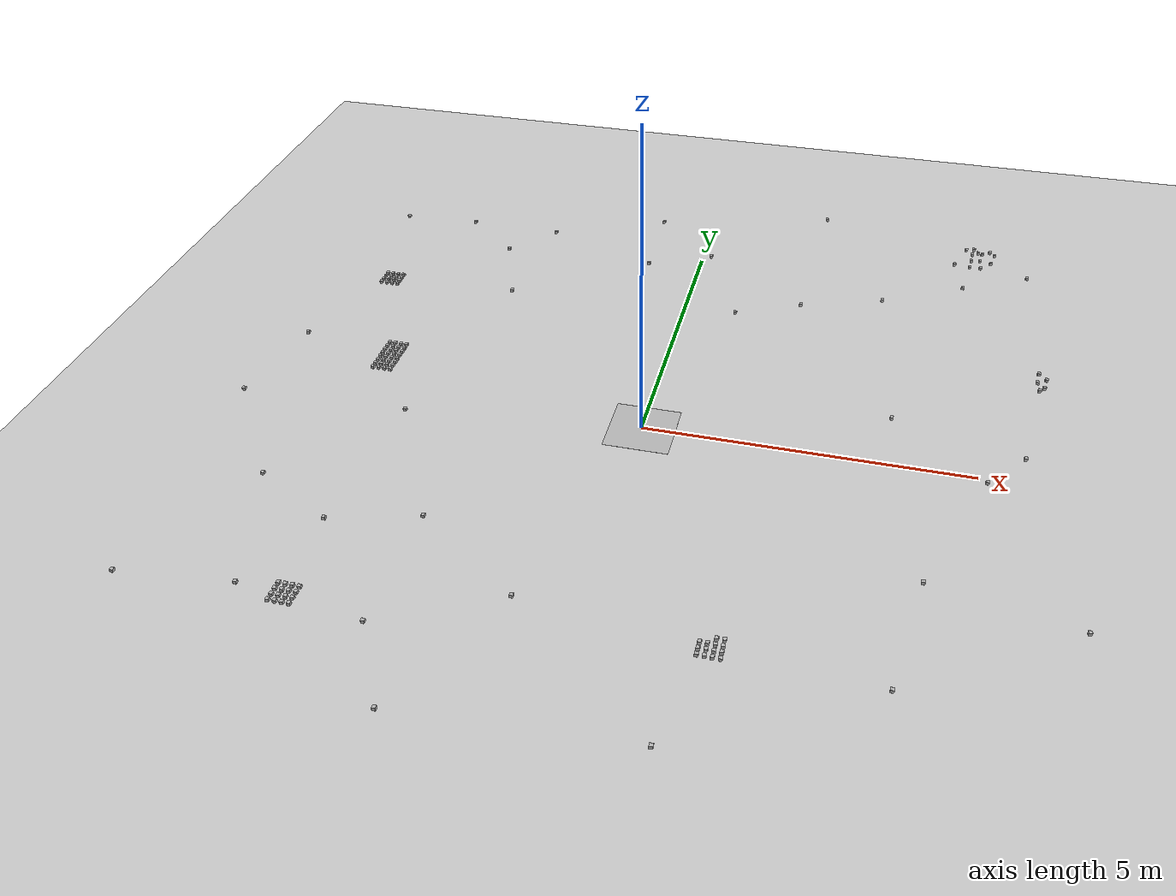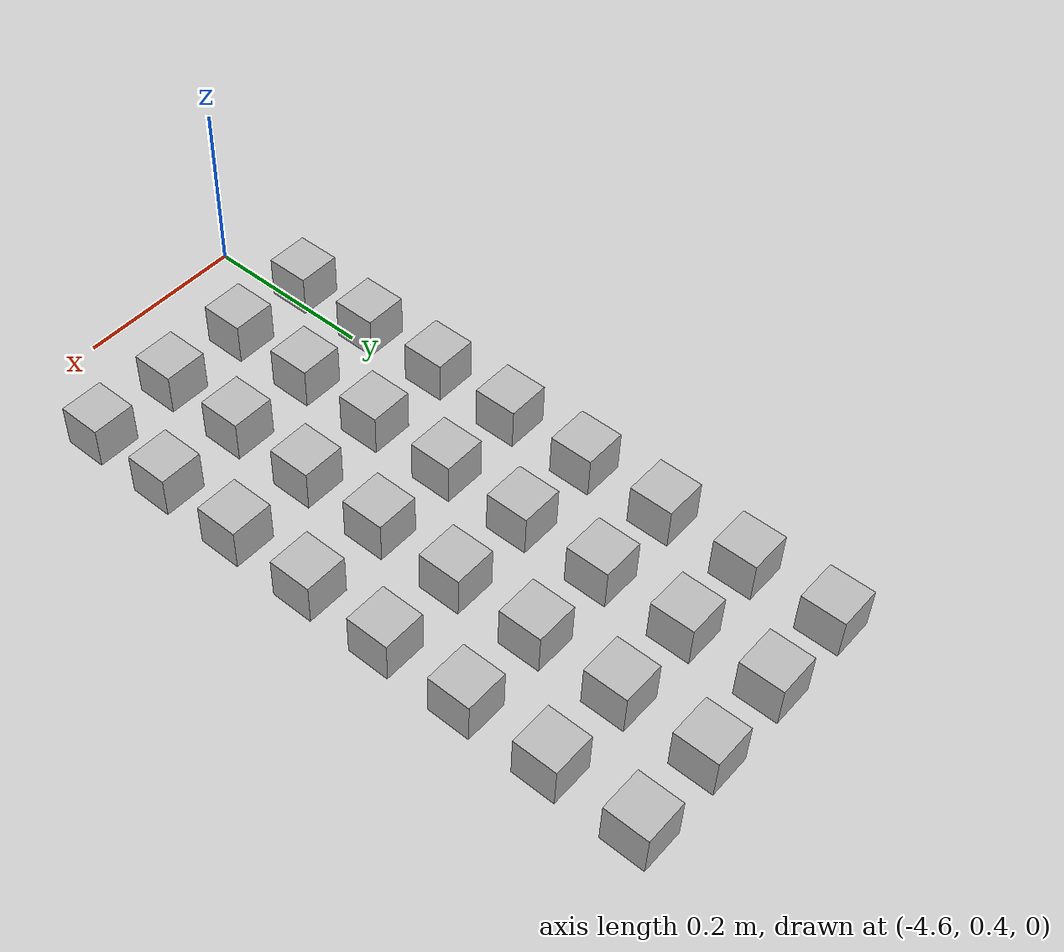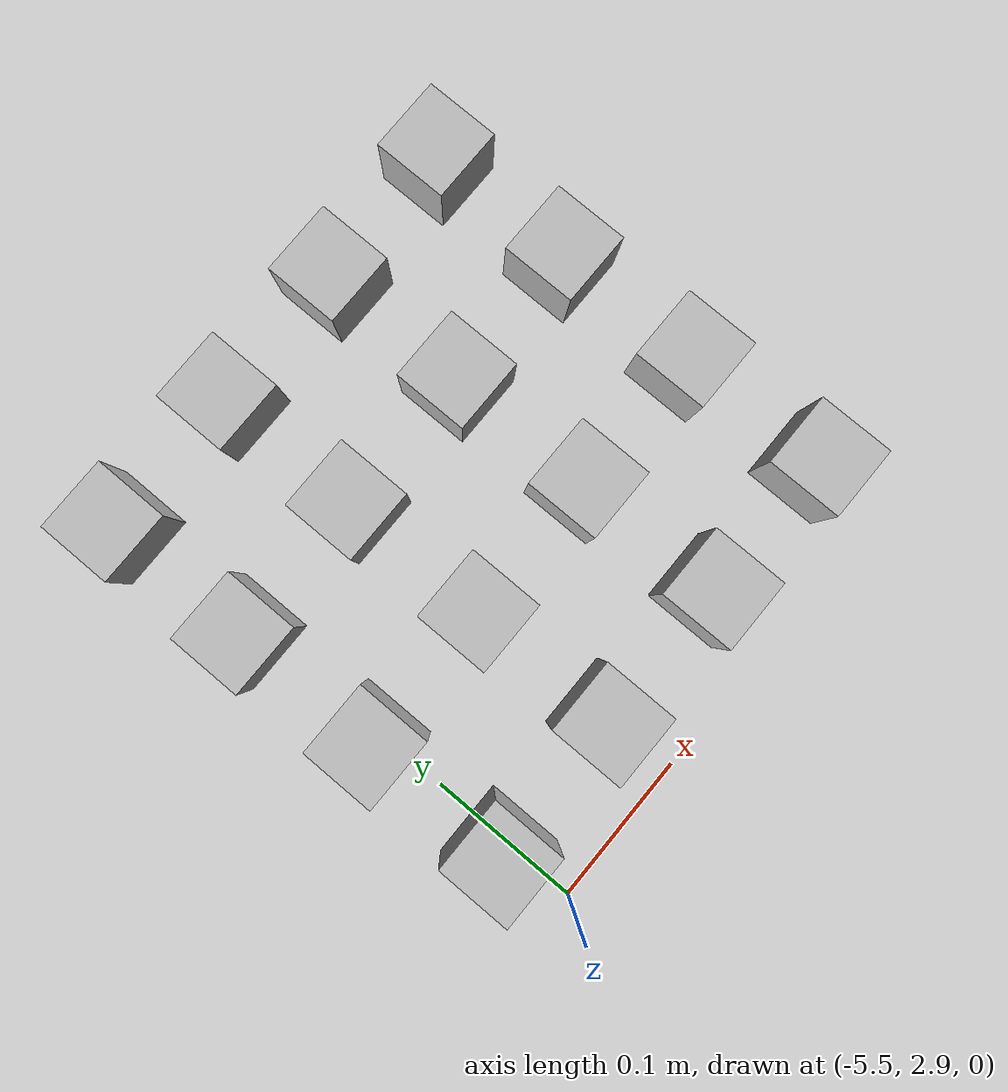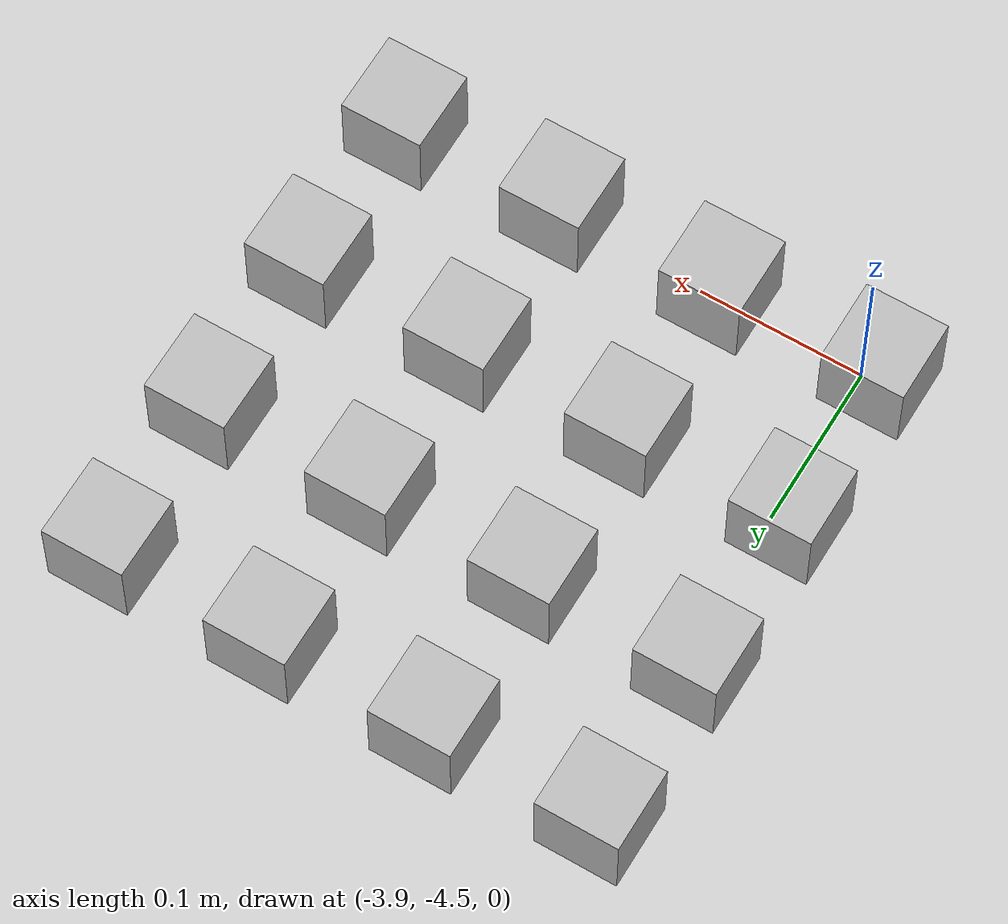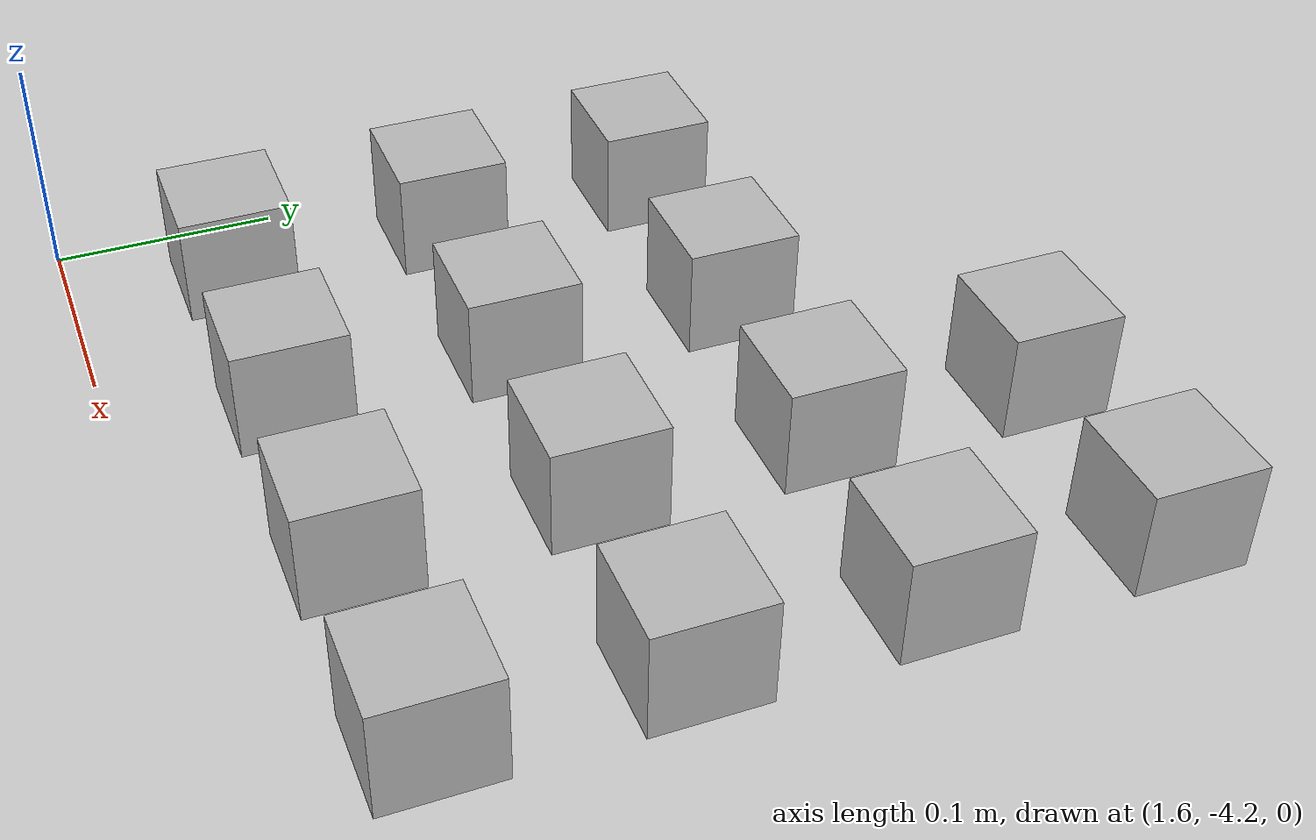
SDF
<sdf version="1.6">
 <world name="default">
  <model name="ground_plane">
   <static>1</static>
   <link name="link">
    <collision name="collision">
     <geometry><plane><normal>0 0 1</normal><size>100 100</size></plane></geometry>
     <surface><friction><ode><mu>100</mu><mu2>50</mu2></ode></friction></surface>
    </collision>
    <visual name="visual">
     <cast_shadows>0</cast_shadows>
     <geometry><plane><normal>0 0 1</normal><size>100 100</size></plane></geometry>
     <material>
      <script><uri>file://media/materials/scripts/gazebo.material</uri><name>Gazebo/Grey</name></script>
     </material>
    </visual>
   </link>
  </model>
  <light name="sun" type="directional">
   <pose>0 0 10 0 -0 0</pose>
   <diffuse>0.8 0.8 0.8 1</diffuse>
   <specular>0.1 0.1 0.1 1</specular>
   <attenuation>
    <range>1000</range>
    <constant>0.9</constant>
    <linear>0.01</linear>
    <quadratic>0.001</quadratic>
   </attenuation>
   <direction>-0.5 0.5 -1</direction>
  </light>
  <plugin name="SetupWorld" filename="libgazebo_plugins.so"/>
  <gravity>0 0 -9.8</gravity>
  <magnetic_field>6e-06 2.3e-05 -4.2e-05</magnetic_field>
  <atmosphere type="adiabatic"/>
  <physics name="default_physics" default="0" type="ode">
   <max_step_size>0.001</max_step_size>
   <real_time_factor>1</real_time_factor>
   <real_time_update_rate>1000</real_time_update_rate>
  </physics>
  <scene><ambient>0.4 0.4 0.4 1</ambient><background>0.7 0.7 0.7 1</background><shadows>1</shadows></scene>
  <spherical_coordinates>
   <surface_model>EARTH_WGS84</surface_model>
   <latitude_deg>0</latitude_deg>
   <longitude_deg>0</longitude_deg>
   <elevation>0</elevation>
   <heading_deg>0</heading_deg>
  </spherical_coordinates>
  <model name="at0">
   <static>0</static>
   <link name="link">
    <inertial>
     <mass>0.01</mass>
     <inertia><ixx>4e-05</ixx><ixy>0</ixy><ixz>0</ixz><iyy>4e-05</iyy><iyz>0</iyz><izz>4e-05</izz></inertia>
    </inertial>
    <visual name="visual">
     <geometry><box><size>0.05 0.05 0.05</size></box></geometry>
     <material>
      <script>
       <uri>model://at0/materials/scripts</uri>
       <uri>model://at0/materials/textures</uri>
       <name>at0/Diffuse</name>
      </script>
     </material>
    </visual>
    <collision name="collision">
     <geometry><box><size>0.05 0.05 0.05</size></box></geometry>
     <surface><friction><ode><mu>0.8</mu><mu2>0.7</mu2></ode></friction></surface>
    </collision>
   </link>
   <pose>-4.61833 0.509652 0.025 0 -0 0</pose>
  </model>
  <model name="at1">
   <static>0</static>
   <link name="link">
    <inertial>
     <mass>0.01</mass>
     <inertia><ixx>4e-05</ixx><ixy>0</ixy><ixz>0</ixz><iyy>4e-05</iyy><iyz>0</iyz><izz>4e-05</izz></inertia>
    </inertial>
    <visual name="visual">
     <geometry><box><size>0.05 0.05 0.05</size></box></geometry>
     <material>
      <script>
       <uri>model://at0/materials/scripts</uri>
       <uri>model://at0/materials/textures</uri>
       <name>at0/Diffuse</name>
      </script>
     </material>
    </visual>
    <collision name="collision">
     <geometry><box><size>0.05 0.05 0.05</size></box></geometry>
     <surface><friction><ode><mu>0.8</mu><mu2>0.7</mu2></ode></friction></surface>
    </collision>
   </link>
   <pose>-4.51833 0.509652 0.025 0 -0 0</pose>
  </model>
  <model name="at2">
   <static>0</static>
   <link name="link">
    <inertial>
     <mass>0.01</mass>
     <inertia><ixx>4e-05</ixx><ixy>0</ixy><ixz>0</ixz><iyy>4e-05</iyy><iyz>0</iyz><izz>4e-05</izz></inertia>
    </inertial>
    <visual name="visual">
     <geometry><box><size>0.05 0.05 0.05</size></box></geometry>
     <material>
      <script>
       <uri>model://at0/materials/scripts</uri>
       <uri>model://at0/materials/textures</uri>
       <name>at0/Diffuse</name>
      </script>
     </material>
    </visual>
    <collision name="collision">
     <geometry><box><size>0.05 0.05 0.05</size></box></geometry>
     <surface><friction><ode><mu>0.8</mu><mu2>0.7</mu2></ode></friction></surface>
    </collision>
   </link>
   <pose>-4.41833 0.509652 0.025 0 -0 0</pose>
  </model>
  <model name="at3">
   <static>0</static>
   <link name="link">
    <inertial>
     <mass>0.01</mass>
     <inertia><ixx>4e-05</ixx><ixy>0</ixy><ixz>0</ixz><iyy>4e-05</iyy><iyz>0</iyz><izz>4e-05</izz></inertia>
    </inertial>
    <visual name="visual">
     <geometry><box><size>0.05 0.05 0.05</size></box></geometry>
     <material>
      <script>
       <uri>model://at0/materials/scripts</uri>
       <uri>model://at0/materials/textures</uri>
       <name>at0/Diffuse</name>
      </script>
     </material>
    </visual>
    <collision name="collision">
     <geometry><box><size>0.05 0.05 0.05</size></box></geometry>
     <surface><friction><ode><mu>0.8</mu><mu2>0.7</mu2></ode></friction></surface>
    </collision>
   </link>
   <pose>-4.31833 0.509652 0.025 0 -0 0</pose>
  </model>
  <model name="at4">
   <static>0</static>
   <link name="link">
    <inertial>
     <mass>0.01</mass>
     <inertia><ixx>4e-05</ixx><ixy>0</ixy><ixz>0</ixz><iyy>4e-05</iyy><iyz>0</iyz><izz>4e-05</izz></inertia>
    </inertial>
    <visual name="visual">
     <geometry><box><size>0.05 0.05 0.05</size></box></geometry>
     <material>
      <script>
       <uri>model://at0/materials/scripts</uri>
       <uri>model://at0/materials/textures</uri>
       <name>at0/Diffuse</name>
      </script>
     </material>
    </visual>
    <collision name="collision">
     <geometry><box><size>0.05 0.05 0.05</size></box></geometry>
     <surface><friction><ode><mu>0.8</mu><mu2>0.7</mu2></ode></friction></surface>
    </collision>
   </link>
   <pose>-4.61833 0.609652 0.025 0 -0 0</pose>
  </model>
  <model name="at5">
   <static>0</static>
   <link name="link">
    <inertial>
     <mass>0.01</mass>
     <inertia><ixx>4e-05</ixx><ixy>0</ixy><ixz>0</ixz><iyy>4e-05</iyy><iyz>0</iyz><izz>4e-05</izz></inertia>
    </inertial>
    <visual name="visual">
     <geometry><box><size>0.05 0.05 0.05</size></box></geometry>
     <material>
      <script>
       <uri>model://at0/materials/scripts</uri>
       <uri>model://at0/materials/textures</uri>
       <name>at0/Diffuse</name>
      </script>
     </material>
    </visual>
    <collision name="collision">
     <geometry><box><size>0.05 0.05 0.05</size></box></geometry>
     <surface><friction><ode><mu>0.8</mu><mu2>0.7</mu2></ode></friction></surface>
    </collision>
   </link>
   <pose>-4.51833 0.609652 0.025 0 -0 0</pose>
  </model>
  <model name="at6">
   <static>0</static>
   <link name="link">
    <inertial>
     <mass>0.01</mass>
     <inertia><ixx>4e-05</ixx><ixy>0</ixy><ixz>0</ixz><iyy>4e-05</iyy><iyz>0</iyz><izz>4e-05</izz></inertia>
    </inertial>
    <visual name="visual">
     <geometry><box><size>0.05 0.05 0.05</size></box></geometry>
     <material>
      <script>
       <uri>model://at0/materials/scripts</uri>
       <uri>model://at0/materials/textures</uri>
       <name>at0/Diffuse</name>
      </script>
     </material>
    </visual>
    <collision name="collision">
     <geometry><box><size>0.05 0.05 0.05</size></box></geometry>
     <surface><friction><ode><mu>0.8</mu><mu2>0.7</mu2></ode></friction></surface>
    </collision>
   </link>
   <pose>-4.41833 0.609652 0.025 0 -0 0</pose>
  </model>
  <model name="at7">
   <static>0</static>
   <link name="link">
    <inertial>
     <mass>0.01</mass>
     <inertia><ixx>4e-05</ixx><ixy>0</ixy><ixz>0</ixz><iyy>4e-05</iyy><iyz>0</iyz><izz>4e-05</izz></inertia>
    </inertial>
    <visual name="visual">
     <geometry><box><size>0.05 0.05 0.05</size></box></geometry>
     <material>
      <script>
       <uri>model://at0/materials/scripts</uri>
       <uri>model://at0/materials/textures</uri>
       <name>at0/Diffuse</name>
      </script>
     </material>
    </visual>
    <collision name="collision">
     <geometry><box><size>0.05 0.05 0.05</size></box></geometry>
     <surface><friction><ode><mu>0.8</mu><mu2>0.7</mu2></ode></friction></surface>
    </collision>
   </link>
   <pose>-4.31833 0.609652 0.025 0 -0 0</pose>
  </model>
  <model name="at8">
   <static>0</static>
   <link name="link">
    <inertial>
     <mass>0.01</mass>
     <inertia><ixx>4e-05</ixx><ixy>0</ixy><ixz>0</ixz><iyy>4e-05</iyy><iyz>0</iyz><izz>4e-05</izz></inertia>
    </inertial>
    <visual name="visual">
     <geometry><box><size>0.05 0.05 0.05</size></box></geometry>
     <material>
      <script>
       <uri>model://at0/materials/scripts</uri>
       <uri>model://at0/materials/textures</uri>
       <name>at0/Diffuse</name>
      </script>
     </material>
    </visual>
    <collision name="collision">
     <geometry><box><size>0.05 0.05 0.05</size></box></geometry>
     <surface><friction><ode><mu>0.8</mu><mu2>0.7</mu2></ode></friction></surface>
    </collision>
   </link>
   <pose>-4.61833 0.709652 0.025 0 -0 0</pose>
  </model>
  <model name="at9">
   <static>0</static>
   <link name="link">
    <inertial>
     <mass>0.01</mass>
     <inertia><ixx>4e-05</ixx><ixy>0</ixy><ixz>0</ixz><iyy>4e-05</iyy><iyz>0</iyz><izz>4e-05</izz></inertia>
    </inertial>
    <visual name="visual">
     <geometry><box><size>0.05 0.05 0.05</size></box></geometry>
     <material>
      <script>
       <uri>model://at0/materials/scripts</uri>
       <uri>model://at0/materials/textures</uri>
       <name>at0/Diffuse</name>
      </script>
     </material>
    </visual>
    <collision name="collision">
     <geometry><box><size>0.05 0.05 0.05</size></box></geometry>
     <surface><friction><ode><mu>0.8</mu><mu2>0.7</mu2></ode></friction></surface>
    </collision>
   </link>
   <pose>-4.51833 0.709652 0.025 0 -0 0</pose>
  </model>
  <model name="at10">
   <static>0</static>
   <link name="link">
    <inertial>
     <mass>0.01</mass>
     <inertia><ixx>4e-05</ixx><ixy>0</ixy><ixz>0</ixz><iyy>4e-05</iyy><iyz>0</iyz><izz>4e-05</izz></inertia>
    </inertial>
    <visual name="visual">
     <geometry><box><size>0.05 0.05 0.05</size></box></geometry>
     <material>
      <script>
       <uri>model://at0/materials/scripts</uri>
       <uri>model://at0/materials/textures</uri>
       <name>at0/Diffuse</name>
      </script>
     </material>
    </visual>
    <collision name="collision">
     <geometry><box><size>0.05 0.05 0.05</size></box></geometry>
     <surface><friction><ode><mu>0.8</mu><mu2>0.7</mu2></ode></friction></surface>
    </collision>
   </link>
   <pose>-4.41833 0.709652 0.025 0 -0 0</pose>
  </model>
  <model name="at11">
   <static>0</static>
   <link name="link">
    <inertial>
     <mass>0.01</mass>
     <inertia><ixx>4e-05</ixx><ixy>0</ixy><ixz>0</ixz><iyy>4e-05</iyy><iyz>0</iyz><izz>4e-05</izz></inertia>
    </inertial>
    <visual name="visual">
     <geometry><box><size>0.05 0.05 0.05</size></box></geometry>
     <material>
      <script>
       <uri>model://at0/materials/scripts</uri>
       <uri>model://at0/materials/textures</uri>
       <name>at0/Diffuse</name>
      </script>
     </material>
    </visual>
    <collision name="collision">
     <geometry><box><size>0.05 0.05 0.05</size></box></geometry>
     <surface><friction><ode><mu>0.8</mu><mu2>0.7</mu2></ode></friction></surface>
    </collision>
   </link>
   <pose>-4.31833 0.709652 0.025 0 -0 0</pose>
  </model>
  <model name="at12">
   <static>0</static>
   <link name="link">
    <inertial>
     <mass>0.01</mass>
     <inertia><ixx>4e-05</ixx><ixy>0</ixy><ixz>0</ixz><iyy>4e-05</iyy><iyz>0</iyz><izz>4e-05</izz></inertia>
    </inertial>
    <visual name="visual">
     <geometry><box><size>0.05 0.05 0.05</size></box></geometry>
     <material>
      <script>
       <uri>model://at0/materials/scripts</uri>
       <uri>model://at0/materials/textures</uri>
       <name>at0/Diffuse</name>
      </script>
     </material>
    </visual>
    <collision name="collision">
     <geometry><box><size>0.05 0.05 0.05</size></box></geometry>
     <surface><friction><ode><mu>0.8</mu><mu2>0.7</mu2></ode></friction></surface>
    </collision>
   </link>
   <pose>-4.61833 0.809652 0.025 0 -0 0</pose>
  </model>
  <model name="at13">
   <static>0</static>
   <link name="link">
    <inertial>
     <mass>0.01</mass>
     <inertia><ixx>4e-05</ixx><ixy>0</ixy><ixz>0</ixz><iyy>4e-05</iyy><iyz>0</iyz><izz>4e-05</izz></inertia>
    </inertial>
    <visual name="visual">
     <geometry><box><size>0.05 0.05 0.05</size></box></geometry>
     <material>
      <script>
       <uri>model://at0/materials/scripts</uri>
       <uri>model://at0/materials/textures</uri>
       <name>at0/Diffuse</name>
      </script>
     </material>
    </visual>
    <collision name="collision">
     <geometry><box><size>0.05 0.05 0.05</size></box></geometry>
     <surface><friction><ode><mu>0.8</mu><mu2>0.7</mu2></ode></friction></surface>
    </collision>
   </link>
   <pose>-4.51833 0.809652 0.025 0 -0 0</pose>
  </model>
  <model name="at14">
   <static>0</static>
   <link name="link">
    <inertial>
     <mass>0.01</mass>
     <inertia><ixx>4e-05</ixx><ixy>0</ixy><ixz>0</ixz><iyy>4e-05</iyy><iyz>0</iyz><izz>4e-05</izz></inertia>
    </inertial>
    <visual name="visual">
     <geometry><box><size>0.05 0.05 0.05</size></box></geometry>
     <material>
      <script>
       <uri>model://at0/materials/scripts</uri>
       <uri>model://at0/materials/textures</uri>
       <name>at0/Diffuse</name>
      </script>
     </material>
    </visual>
    <collision name="collision">
     <geometry><box><size>0.05 0.05 0.05</size></box></geometry>
     <surface><friction><ode><mu>0.8</mu><mu2>0.7</mu2></ode></friction></surface>
    </collision>
   </link>
   <pose>-4.41833 0.809652 0.025 0 -0 0</pose>
  </model>
  <model name="at15">
   <static>0</static>
   <link name="link">
    <inertial>
     <mass>0.01</mass>
     <inertia><ixx>4e-05</ixx><ixy>0</ixy><ixz>0</ixz><iyy>4e-05</iyy><iyz>0</iyz><izz>4e-05</izz></inertia>
    </inertial>
    <visual name="visual">
     <geometry><box><size>0.05 0.05 0.05</size></box></geometry>
     <material>
      <script>
       <uri>model://at0/materials/scripts</uri>
       <uri>model://at0/materials/textures</uri>
       <name>at0/Diffuse</name>
      </script>
     </material>
    </visual>
    <collision name="collision">
     <geometry><box><size>0.05 0.05 0.05</size></box></geometry>
     <surface><friction><ode><mu>0.8</mu><mu2>0.7</mu2></ode></friction></surface>
    </collision>
   </link>
   <pose>-4.31833 0.809652 0.025 0 -0 0</pose>
  </model>
  <model name="at16">
   <static>0</static>
   <link name="link">
    <inertial>
     <mass>0.01</mass>
     <inertia><ixx>4e-05</ixx><ixy>0</ixy><ixz>0</ixz><iyy>4e-05</iyy><iyz>0</iyz><izz>4e-05</izz></inertia>
    </inertial>
    <visual name="visual">
     <geometry><box><size>0.05 0.05 0.05</size></box></geometry>
     <material>
      <script>
       <uri>model://at0/materials/scripts</uri>
       <uri>model://at0/materials/textures</uri>
       <name>at0/Diffuse</name>
      </script>
     </material>
    </visual>
    <collision name="collision">
     <geometry><box><size>0.05 0.05 0.05</size></box></geometry>
     <surface><friction><ode><mu>0.8</mu><mu2>0.7</mu2></ode></friction></surface>
    </collision>
   </link>
   <pose>-4.61833 0.909652 0.025 0 -0 0</pose>
  </model>
  <model name="at17">
   <static>0</static>
   <link name="link">
    <inertial>
     <mass>0.01</mass>
     <inertia><ixx>4e-05</ixx><ixy>0</ixy><ixz>0</ixz><iyy>4e-05</iyy><iyz>0</iyz><izz>4e-05</izz></inertia>
    </inertial>
    <visual name="visual">
     <geometry><box><size>0.05 0.05 0.05</size></box></geometry>
     <material>
      <script>
       <uri>model://at0/materials/scripts</uri>
       <uri>model://at0/materials/textures</uri>
       <name>at0/Diffuse</name>
      </script>
     </material>
    </visual>
    <collision name="collision">
     <geometry><box><size>0.05 0.05 0.05</size></box></geometry>
     <surface><friction><ode><mu>0.8</mu><mu2>0.7</mu2></ode></friction></surface>
    </collision>
   </link>
   <pose>-4.51833 0.909652 0.025 0 -0 0</pose>
  </model>
  <model name="at18">
   <static>0</static>
   <link name="link">
    <inertial>
     <mass>0.01</mass>
     <inertia><ixx>4e-05</ixx><ixy>0</ixy><ixz>0</ixz><iyy>4e-05</iyy><iyz>0</iyz><izz>4e-05</izz></inertia>
    </inertial>
    <visual name="visual">
     <geometry><box><size>0.05 0.05 0.05</size></box></geometry>
     <material>
      <script>
       <uri>model://at0/materials/scripts</uri>
       <uri>model://at0/materials/textures</uri>
       <name>at0/Diffuse</name>
      </script>
     </material>
    </visual>
    <collision name="collision">
     <geometry><box><size>0.05 0.05 0.05</size></box></geometry>
     <surface><friction><ode><mu>0.8</mu><mu2>0.7</mu2></ode></friction></surface>
    </collision>
   </link>
   <pose>-4.41833 0.909652 0.025 0 -0 0</pose>
  </model>
  <model name="at19">
   <static>0</static>
   <link name="link">
    <inertial>
     <mass>0.01</mass>
     <inertia><ixx>4e-05</ixx><ixy>0</ixy><ixz>0</ixz><iyy>4e-05</iyy><iyz>0</iyz><izz>4e-05</izz></inertia>
    </inertial>
    <visual name="visual">
     <geometry><box><size>0.05 0.05 0.05</size></box></geometry>
     <material>
      <script>
       <uri>model://at0/materials/scripts</uri>
       <uri>model://at0/materials/textures</uri>
       <name>at0/Diffuse</name>
      </script>
     </material>
    </visual>
    <collision name="collision">
     <geometry><box><size>0.05 0.05 0.05</size></box></geometry>
     <surface><friction><ode><mu>0.8</mu><mu2>0.7</mu2></ode></friction></surface>
    </collision>
   </link>
   <pose>-4.31833 0.909652 0.025 0 -0 0</pose>
  </model>
  <model name="at20">
   <static>0</static>
   <link name="link">
    <inertial>
     <mass>0.01</mass>
     <inertia><ixx>4e-05</ixx><ixy>0</ixy><ixz>0</ixz><iyy>4e-05</iyy><iyz>0</iyz><izz>4e-05</izz></inertia>
    </inertial>
    <visual name="visual">
     <geometry><box><size>0.05 0.05 0.05</size></box></geometry>
     <material>
      <script>
       <uri>model://at0/materials/scripts</uri>
       <uri>model://at0/materials/textures</uri>
       <name>at0/Diffuse</name>
      </script>
     </material>
    </visual>
    <collision name="collision">
     <geometry><box><size>0.05 0.05 0.05</size></box></geometry>
     <surface><friction><ode><mu>0.8</mu><mu2>0.7</mu2></ode></friction></surface>
    </collision>
   </link>
   <pose>-4.61833 1.00965 0.025 0 -0 0</pose>
  </model>
  <model name="at21">
   <static>0</static>
   <link name="link">
    <inertial>
     <mass>0.01</mass>
     <inertia><ixx>4e-05</ixx><ixy>0</ixy><ixz>0</ixz><iyy>4e-05</iyy><iyz>0</iyz><izz>4e-05</izz></inertia>
    </inertial>
    <visual name="visual">
     <geometry><box><size>0.05 0.05 0.05</size></box></geometry>
     <material>
      <script>
       <uri>model://at0/materials/scripts</uri>
       <uri>model://at0/materials/textures</uri>
       <name>at0/Diffuse</name>
      </script>
     </material>
    </visual>
    <collision name="collision">
     <geometry><box><size>0.05 0.05 0.05</size></box></geometry>
     <surface><friction><ode><mu>0.8</mu><mu2>0.7</mu2></ode></friction></surface>
    </collision>
   </link>
   <pose>-4.51833 1.00965 0.025 0 -0 0</pose>
  </model>
  <model name="at22">
   <static>0</static>
   <link name="link">
    <inertial>
     <mass>0.01</mass>
     <inertia><ixx>4e-05</ixx><ixy>0</ixy><ixz>0</ixz><iyy>4e-05</iyy><iyz>0</iyz><izz>4e-05</izz></inertia>
    </inertial>
    <visual name="visual">
     <geometry><box><size>0.05 0.05 0.05</size></box></geometry>
     <material>
      <script>
       <uri>model://at0/materials/scripts</uri>
       <uri>model://at0/materials/textures</uri>
       <name>at0/Diffuse</name>
      </script>
     </material>
    </visual>
    <collision name="collision">
     <geometry><box><size>0.05 0.05 0.05</size></box></geometry>
     <surface><friction><ode><mu>0.8</mu><mu2>0.7</mu2></ode></friction></surface>
    </collision>
   </link>
   <pose>-4.41833 1.00965 0.025 0 -0 0</pose>
  </model>
  <model name="at23">
   <static>0</static>
   <link name="link">
    <inertial>
     <mass>0.01</mass>
     <inertia><ixx>4e-05</ixx><ixy>0</ixy><ixz>0</ixz><iyy>4e-05</iyy><iyz>0</iyz><izz>4e-05</izz></inertia>
    </inertial>
    <visual name="visual">
     <geometry><box><size>0.05 0.05 0.05</size></box></geometry>
     <material>
      <script>
       <uri>model://at0/materials/scripts</uri>
       <uri>model://at0/materials/textures</uri>
       <name>at0/Diffuse</name>
      </script>
     </material>
    </visual>
    <collision name="collision">
     <geometry><box><size>0.05 0.05 0.05</size></box></geometry>
     <surface><friction><ode><mu>0.8</mu><mu2>0.7</mu2></ode></friction></surface>
    </collision>
   </link>
   <pose>-4.31833 1.00965 0.025 0 -0 0</pose>
  </model>
  <model name="at24">
   <static>0</static>
   <link name="link">
    <inertial>
     <mass>0.01</mass>
     <inertia><ixx>4e-05</ixx><ixy>0</ixy><ixz>0</ixz><iyy>4e-05</iyy><iyz>0</iyz><izz>4e-05</izz></inertia>
    </inertial>
    <visual name="visual">
     <geometry><box><size>0.05 0.05 0.05</size></box></geometry>
     <material>
      <script>
       <uri>model://at0/materials/scripts</uri>
       <uri>model://at0/materials/textures</uri>
       <name>at0/Diffuse</name>
      </script>
     </material>
    </visual>
    <collision name="collision">
     <geometry><box><size>0.05 0.05 0.05</size></box></geometry>
     <surface><friction><ode><mu>0.8</mu><mu2>0.7</mu2></ode></friction></surface>
    </collision>
   </link>
   <pose>-4.61833 1.10965 0.025 0 -0 0</pose>
  </model>
  <model name="at25">
   <static>0</static>
   <link name="link">
    <inertial>
     <mass>0.01</mass>
     <inertia><ixx>4e-05</ixx><ixy>0</ixy><ixz>0</ixz><iyy>4e-05</iyy><iyz>0</iyz><izz>4e-05</izz></inertia>
    </inertial>
    <visual name="visual">
     <geometry><box><size>0.05 0.05 0.05</size></box></geometry>
     <material>
      <script>
       <uri>model://at0/materials/scripts</uri>
       <uri>model://at0/materials/textures</uri>
       <name>at0/Diffuse</name>
      </script>
     </material>
    </visual>
    <collision name="collision">
     <geometry><box><size>0.05 0.05 0.05</size></box></geometry>
     <surface><friction><ode><mu>0.8</mu><mu2>0.7</mu2></ode></friction></surface>
    </collision>
   </link>
   <pose>-4.51833 1.10965 0.025 0 -0 0</pose>
  </model>
  <model name="at26">
   <static>0</static>
   <link name="link">
    <inertial>
     <mass>0.01</mass>
     <inertia><ixx>4e-05</ixx><ixy>0</ixy><ixz>0</ixz><iyy>4e-05</iyy><iyz>0</iyz><izz>4e-05</izz></inertia>
    </inertial>
    <visual name="visual">
     <geometry><box><size>0.05 0.05 0.05</size></box></geometry>
     <material>
      <script>
       <uri>model://at0/materials/scripts</uri>
       <uri>model://at0/materials/textures</uri>
       <name>at0/Diffuse</name>
      </script>
     </material>
    </visual>
    <collision name="collision">
     <geometry><box><size>0.05 0.05 0.05</size></box></geometry>
     <surface><friction><ode><mu>0.8</mu><mu2>0.7</mu2></ode></friction></surface>
    </collision>
   </link>
   <pose>-4.41833 1.10965 0.025 0 -0 0</pose>
  </model>
  <model name="at27">
   <static>0</static>
   <link name="link">
    <inertial>
     <mass>0.01</mass>
     <inertia><ixx>4e-05</ixx><ixy>0</ixy><ixz>0</ixz><iyy>4e-05</iyy><iyz>0</iyz><izz>4e-05</izz></inertia>
    </inertial>
    <visual name="visual">
     <geometry><box><size>0.05 0.05 0.05</size></box></geometry>
     <material>
      <script>
       <uri>model://at0/materials/scripts</uri>
       <uri>model://at0/materials/textures</uri>
       <name>at0/Diffuse</name>
      </script>
     </material>
    </visual>
    <collision name="collision">
     <geometry><box><size>0.05 0.05 0.05</size></box></geometry>
     <surface><friction><ode><mu>0.8</mu><mu2>0.7</mu2></ode></friction></surface>
    </collision>
   </link>
   <pose>-4.31833 1.10965 0.025 0 -0 0</pose>
  </model>
  <model name="at28">
   <static>0</static>
   <link name="link">
    <inertial>
     <mass>0.01</mass>
     <inertia><ixx>4e-05</ixx><ixy>0</ixy><ixz>0</ixz><iyy>4e-05</iyy><iyz>0</iyz><izz>4e-05</izz></inertia>
    </inertial>
    <visual name="visual">
     <geometry><box><size>0.05 0.05 0.05</size></box></geometry>
     <material>
      <script>
       <uri>model://at0/materials/scripts</uri>
       <uri>model://at0/materials/textures</uri>
       <name>at0/Diffuse</name>
      </script>
     </material>
    </visual>
    <collision name="collision">
     <geometry><box><size>0.05 0.05 0.05</size></box></geometry>
     <surface><friction><ode><mu>0.8</mu><mu2>0.7</mu2></ode></friction></surface>
    </collision>
   </link>
   <pose>-4.61833 1.20965 0.025 0 -0 0</pose>
  </model>
  <model name="at29">
   <static>0</static>
   <link name="link">
    <inertial>
     <mass>0.01</mass>
     <inertia><ixx>4e-05</ixx><ixy>0</ixy><ixz>0</ixz><iyy>4e-05</iyy><iyz>0</iyz><izz>4e-05</izz></inertia>
    </inertial>
    <visual name="visual">
     <geometry><box><size>0.05 0.05 0.05</size></box></geometry>
     <material>
      <script>
       <uri>model://at0/materials/scripts</uri>
       <uri>model://at0/materials/textures</uri>
       <name>at0/Diffuse</name>
      </script>
     </material>
    </visual>
    <collision name="collision">
     <geometry><box><size>0.05 0.05 0.05</size></box></geometry>
     <surface><friction><ode><mu>0.8</mu><mu2>0.7</mu2></ode></friction></surface>
    </collision>
   </link>
   <pose>-4.51833 1.20965 0.025 0 -0 0</pose>
  </model>
  <model name="at30">
   <static>0</static>
   <link name="link">
    <inertial>
     <mass>0.01</mass>
     <inertia><ixx>4e-05</ixx><ixy>0</ixy><ixz>0</ixz><iyy>4e-05</iyy><iyz>0</iyz><izz>4e-05</izz></inertia>
    </inertial>
    <visual name="visual">
     <geometry><box><size>0.05 0.05 0.05</size></box></geometry>
     <material>
      <script>
       <uri>model://at0/materials/scripts</uri>
       <uri>model://at0/materials/textures</uri>
       <name>at0/Diffuse</name>
      </script>
     </material>
    </visual>
    <collision name="collision">
     <geometry><box><size>0.05 0.05 0.05</size></box></geometry>
     <surface><friction><ode><mu>0.8</mu><mu2>0.7</mu2></ode></friction></surface>
    </collision>
   </link>
   <pose>-4.41833 1.20965 0.025 0 -0 0</pose>
  </model>
  <model name="at31">
   <static>0</static>
   <link name="link">
    <inertial>
     <mass>0.01</mass>
     <inertia><ixx>4e-05</ixx><ixy>0</ixy><ixz>0</ixz><iyy>4e-05</iyy><iyz>0</iyz><izz>4e-05</izz></inertia>
    </inertial>
    <visual name="visual">
     <geometry><box><size>0.05 0.05 0.05</size></box></geometry>
     <material>
      <script>
       <uri>model://at0/materials/scripts</uri>
       <uri>model://at0/materials/textures</uri>
       <name>at0/Diffuse</name>
      </script>
     </material>
    </visual>
    <collision name="collision">
     <geometry><box><size>0.05 0.05 0.05</size></box></geometry>
     <surface><friction><ode><mu>0.8</mu><mu2>0.7</mu2></ode></friction></surface>
    </collision>
   </link>
   <pose>-4.31833 1.20965 0.025 0 -0 0</pose>
  </model>
  <model name="at32">
   <static>0</static>
   <link name="link">
    <inertial>
     <mass>0.01</mass>
     <inertia><ixx>4e-05</ixx><ixy>0</ixy><ixz>0</ixz><iyy>4e-05</iyy><iyz>0</iyz><izz>4e-05</izz></inertia>
    </inertial>
    <visual name="visual">
     <geometry><box><size>0.05 0.05 0.05</size></box></geometry>
     <material>
      <script>
       <uri>model://at0/materials/scripts</uri>
       <uri>model://at0/materials/textures</uri>
       <name>at0/Diffuse</name>
      </script>
     </material>
    </visual>
    <collision name="collision">
     <geometry><box><size>0.05 0.05 0.05</size></box></geometry>
     <surface><friction><ode><mu>0.8</mu><mu2>0.7</mu2></ode></friction></surface>
    </collision>
   </link>
   <pose>-3.91043 -4.50066 0.025 0 -0 0</pose>
  </model>
  <model name="at33">
   <static>0</static>
   <link name="link">
    <inertial>
     <mass>0.01</mass>
     <inertia><ixx>4e-05</ixx><ixy>0</ixy><ixz>0</ixz><iyy>4e-05</iyy><iyz>0</iyz><izz>4e-05</izz></inertia>
    </inertial>
    <visual name="visual">
     <geometry><box><size>0.05 0.05 0.05</size></box></geometry>
     <material>
      <script>
       <uri>model://at0/materials/scripts</uri>
       <uri>model://at0/materials/textures</uri>
       <name>at0/Diffuse</name>
      </script>
     </material>
    </visual>
    <collision name="collision">
     <geometry><box><size>0.05 0.05 0.05</size></box></geometry>
     <surface><friction><ode><mu>0.8</mu><mu2>0.7</mu2></ode></friction></surface>
    </collision>
   </link>
   <pose>-3.81043 -4.50066 0.025 0 -0 0</pose>
  </model>
  <model name="at34">
   <static>0</static>
   <link name="link">
    <inertial>
     <mass>0.01</mass>
     <inertia><ixx>4e-05</ixx><ixy>0</ixy><ixz>0</ixz><iyy>4e-05</iyy><iyz>0</iyz><izz>4e-05</izz></inertia>
    </inertial>
    <visual name="visual">
     <geometry><box><size>0.05 0.05 0.05</size></box></geometry>
     <material>
      <script>
       <uri>model://at0/materials/scripts</uri>
       <uri>model://at0/materials/textures</uri>
       <name>at0/Diffuse</name>
      </script>
     </material>
    </visual>
    <collision name="collision">
     <geometry><box><size>0.05 0.05 0.05</size></box></geometry>
     <surface><friction><ode><mu>0.8</mu><mu2>0.7</mu2></ode></friction></surface>
    </collision>
   </link>
   <pose>-3.71043 -4.50066 0.025 0 -0 0</pose>
  </model>
  <model name="at35">
   <static>0</static>
   <link name="link">
    <inertial>
     <mass>0.01</mass>
     <inertia><ixx>4e-05</ixx><ixy>0</ixy><ixz>0</ixz><iyy>4e-05</iyy><iyz>0</iyz><izz>4e-05</izz></inertia>
    </inertial>
    <visual name="visual">
     <geometry><box><size>0.05 0.05 0.05</size></box></geometry>
     <material>
      <script>
       <uri>model://at0/materials/scripts</uri>
       <uri>model://at0/materials/textures</uri>
       <name>at0/Diffuse</name>
      </script>
     </material>
    </visual>
    <collision name="collision">
     <geometry><box><size>0.05 0.05 0.05</size></box></geometry>
     <surface><friction><ode><mu>0.8</mu><mu2>0.7</mu2></ode></friction></surface>
    </collision>
   </link>
   <pose>-3.61043 -4.50066 0.025 0 -0 0</pose>
  </model>
  <model name="at36">
   <static>0</static>
   <link name="link">
    <inertial>
     <mass>0.01</mass>
     <inertia><ixx>4e-05</ixx><ixy>0</ixy><ixz>0</ixz><iyy>4e-05</iyy><iyz>0</iyz><izz>4e-05</izz></inertia>
    </inertial>
    <visual name="visual">
     <geometry><box><size>0.05 0.05 0.05</size></box></geometry>
     <material>
      <script>
       <uri>model://at0/materials/scripts</uri>
       <uri>model://at0/materials/textures</uri>
       <name>at0/Diffuse</name>
      </script>
     </material>
    </visual>
    <collision name="collision">
     <geometry><box><size>0.05 0.05 0.05</size></box></geometry>
     <surface><friction><ode><mu>0.8</mu><mu2>0.7</mu2></ode></friction></surface>
    </collision>
   </link>
   <pose>-3.91043 -4.40066 0.025 0 -0 0</pose>
  </model>
  <model name="at37">
   <static>0</static>
   <link name="link">
    <inertial>
     <mass>0.01</mass>
     <inertia><ixx>4e-05</ixx><ixy>0</ixy><ixz>0</ixz><iyy>4e-05</iyy><iyz>0</iyz><izz>4e-05</izz></inertia>
    </inertial>
    <visual name="visual">
     <geometry><box><size>0.05 0.05 0.05</size></box></geometry>
     <material>
      <script>
       <uri>model://at0/materials/scripts</uri>
       <uri>model://at0/materials/textures</uri>
       <name>at0/Diffuse</name>
      </script>
     </material>
    </visual>
    <collision name="collision">
     <geometry><box><size>0.05 0.05 0.05</size></box></geometry>
     <surface><friction><ode><mu>0.8</mu><mu2>0.7</mu2></ode></friction></surface>
    </collision>
   </link>
   <pose>-3.81043 -4.40066 0.025 0 -0 0</pose>
  </model>
  <model name="at38">
   <static>0</static>
   <link name="link">
    <inertial>
     <mass>0.01</mass>
     <inertia><ixx>4e-05</ixx><ixy>0</ixy><ixz>0</ixz><iyy>4e-05</iyy><iyz>0</iyz><izz>4e-05</izz></inertia>
    </inertial>
    <visual name="visual">
     <geometry><box><size>0.05 0.05 0.05</size></box></geometry>
     <material>
      <script>
       <uri>model://at0/materials/scripts</uri>
       <uri>model://at0/materials/textures</uri>
       <name>at0/Diffuse</name>
      </script>
     </material>
    </visual>
    <collision name="collision">
     <geometry><box><size>0.05 0.05 0.05</size></box></geometry>
     <surface><friction><ode><mu>0.8</mu><mu2>0.7</mu2></ode></friction></surface>
    </collision>
   </link>
   <pose>-3.71043 -4.40066 0.025 0 -0 0</pose>
  </model>
  <model name="at39">
   <static>0</static>
   <link name="link">
    <inertial>
     <mass>0.01</mass>
     <inertia><ixx>4e-05</ixx><ixy>0</ixy><ixz>0</ixz><iyy>4e-05</iyy><iyz>0</iyz><izz>4e-05</izz></inertia>
    </inertial>
    <visual name="visual">
     <geometry><box><size>0.05 0.05 0.05</size></box></geometry>
     <material>
      <script>
       <uri>model://at0/materials/scripts</uri>
       <uri>model://at0/materials/textures</uri>
       <name>at0/Diffuse</name>
      </script>
     </material>
    </visual>
    <collision name="collision">
     <geometry><box><size>0.05 0.05 0.05</size></box></geometry>
     <surface><friction><ode><mu>0.8</mu><mu2>0.7</mu2></ode></friction></surface>
    </collision>
   </link>
   <pose>-3.61043 -4.40066 0.025 0 -0 0</pose>
  </model>
  <model name="at40">
   <static>0</static>
   <link name="link">
    <inertial>
     <mass>0.01</mass>
     <inertia><ixx>4e-05</ixx><ixy>0</ixy><ixz>0</ixz><iyy>4e-05</iyy><iyz>0</iyz><izz>4e-05</izz></inertia>
    </inertial>
    <visual name="visual">
     <geometry><box><size>0.05 0.05 0.05</size></box></geometry>
     <material>
      <script>
       <uri>model://at0/materials/scripts</uri>
       <uri>model://at0/materials/textures</uri>
       <name>at0/Diffuse</name>
      </script>
     </material>
    </visual>
    <collision name="collision">
     <geometry><box><size>0.05 0.05 0.05</size></box></geometry>
     <surface><friction><ode><mu>0.8</mu><mu2>0.7</mu2></ode></friction></surface>
    </collision>
   </link>
   <pose>-3.91043 -4.30066 0.025 0 -0 0</pose>
  </model>
  <model name="at41">
   <static>0</static>
   <link name="link">
    <inertial>
     <mass>0.01</mass>
     <inertia><ixx>4e-05</ixx><ixy>0</ixy><ixz>0</ixz><iyy>4e-05</iyy><iyz>0</iyz><izz>4e-05</izz></inertia>
    </inertial>
    <visual name="visual">
     <geometry><box><size>0.05 0.05 0.05</size></box></geometry>
     <material>
      <script>
       <uri>model://at0/materials/scripts</uri>
       <uri>model://at0/materials/textures</uri>
       <name>at0/Diffuse</name>
      </script>
     </material>
    </visual>
    <collision name="collision">
     <geometry><box><size>0.05 0.05 0.05</size></box></geometry>
     <surface><friction><ode><mu>0.8</mu><mu2>0.7</mu2></ode></friction></surface>
    </collision>
   </link>
   <pose>-3.81043 -4.30066 0.025 0 -0 0</pose>
  </model>
  <model name="at42">
   <static>0</static>
   <link name="link">
    <inertial>
     <mass>0.01</mass>
     <inertia><ixx>4e-05</ixx><ixy>0</ixy><ixz>0</ixz><iyy>4e-05</iyy><iyz>0</iyz><izz>4e-05</izz></inertia>
    </inertial>
    <visual name="visual">
     <geometry><box><size>0.05 0.05 0.05</size></box></geometry>
     <material>
      <script>
       <uri>model://at0/materials/scripts</uri>
       <uri>model://at0/materials/textures</uri>
       <name>at0/Diffuse</name>
      </script>
     </material>
    </visual>
    <collision name="collision">
     <geometry><box><size>0.05 0.05 0.05</size></box></geometry>
     <surface><friction><ode><mu>0.8</mu><mu2>0.7</mu2></ode></friction></surface>
    </collision>
   </link>
   <pose>-3.71043 -4.30066 0.025 0 -0 0</pose>
  </model>
  <model name="at43">
   <static>0</static>
   <link name="link">
    <inertial>
     <mass>0.01</mass>
     <inertia><ixx>4e-05</ixx><ixy>0</ixy><ixz>0</ixz><iyy>4e-05</iyy><iyz>0</iyz><izz>4e-05</izz></inertia>
    </inertial>
    <visual name="visual">
     <geometry><box><size>0.05 0.05 0.05</size></box></geometry>
     <material>
      <script>
       <uri>model://at0/materials/scripts</uri>
       <uri>model://at0/materials/textures</uri>
       <name>at0/Diffuse</name>
      </script>
     </material>
    </visual>
    <collision name="collision">
     <geometry><box><size>0.05 0.05 0.05</size></box></geometry>
     <surface><friction><ode><mu>0.8</mu><mu2>0.7</mu2></ode></friction></surface>
    </collision>
   </link>
   <pose>-3.61043 -4.30066 0.025 0 -0 0</pose>
  </model>
  <model name="at44">
   <static>0</static>
   <link name="link">
    <inertial>
     <mass>0.01</mass>
     <inertia><ixx>4e-05</ixx><ixy>0</ixy><ixz>0</ixz><iyy>4e-05</iyy><iyz>0</iyz><izz>4e-05</izz></inertia>
    </inertial>
    <visual name="visual">
     <geometry><box><size>0.05 0.05 0.05</size></box></geometry>
     <material>
      <script>
       <uri>model://at0/materials/scripts</uri>
       <uri>model://at0/materials/textures</uri>
       <name>at0/Diffuse</name>
      </script>
     </material>
    </visual>
    <collision name="collision">
     <geometry><box><size>0.05 0.05 0.05</size></box></geometry>
     <surface><friction><ode><mu>0.8</mu><mu2>0.7</mu2></ode></friction></surface>
    </collision>
   </link>
   <pose>-3.91043 -4.20066 0.025 0 -0 0</pose>
  </model>
  <model name="at45">
   <static>0</static>
   <link name="link">
    <inertial>
     <mass>0.01</mass>
     <inertia><ixx>4e-05</ixx><ixy>0</ixy><ixz>0</ixz><iyy>4e-05</iyy><iyz>0</iyz><izz>4e-05</izz></inertia>
    </inertial>
    <visual name="visual">
     <geometry><box><size>0.05 0.05 0.05</size></box></geometry>
     <material>
      <script>
       <uri>model://at0/materials/scripts</uri>
       <uri>model://at0/materials/textures</uri>
       <name>at0/Diffuse</name>
      </script>
     </material>
    </visual>
    <collision name="collision">
     <geometry><box><size>0.05 0.05 0.05</size></box></geometry>
     <surface><friction><ode><mu>0.8</mu><mu2>0.7</mu2></ode></friction></surface>
    </collision>
   </link>
   <pose>-3.81043 -4.20066 0.025 0 -0 0</pose>
  </model>
  <model name="at46">
   <static>0</static>
   <link name="link">
    <inertial>
     <mass>0.01</mass>
     <inertia><ixx>4e-05</ixx><ixy>0</ixy><ixz>0</ixz><iyy>4e-05</iyy><iyz>0</iyz><izz>4e-05</izz></inertia>
    </inertial>
    <visual name="visual">
     <geometry><box><size>0.05 0.05 0.05</size></box></geometry>
     <material>
      <script>
       <uri>model://at0/materials/scripts</uri>
       <uri>model://at0/materials/textures</uri>
       <name>at0/Diffuse</name>
      </script>
     </material>
    </visual>
    <collision name="collision">
     <geometry><box><size>0.05 0.05 0.05</size></box></geometry>
     <surface><friction><ode><mu>0.8</mu><mu2>0.7</mu2></ode></friction></surface>
    </collision>
   </link>
   <pose>-3.71043 -4.20066 0.025 0 -0 0</pose>
  </model>
  <model name="at47">
   <static>0</static>
   <link name="link">
    <inertial>
     <mass>0.01</mass>
     <inertia><ixx>4e-05</ixx><ixy>0</ixy><ixz>0</ixz><iyy>4e-05</iyy><iyz>0</iyz><izz>4e-05</izz></inertia>
    </inertial>
    <visual name="visual">
     <geometry><box><size>0.05 0.05 0.05</size></box></geometry>
     <material>
      <script>
       <uri>model://at0/materials/scripts</uri>
       <uri>model://at0/materials/textures</uri>
       <name>at0/Diffuse</name>
      </script>
     </material>
    </visual>
    <collision name="collision">
     <geometry><box><size>0.05 0.05 0.05</size></box></geometry>
     <surface><friction><ode><mu>0.8</mu><mu2>0.7</mu2></ode></friction></surface>
    </collision>
   </link>
   <pose>-3.61043 -4.20066 0.025 0 -0 0</pose>
  </model>
  <model name="at48">
   <static>0</static>
   <link name="link">
    <inertial>
     <mass>0.01</mass>
     <inertia><ixx>4e-05</ixx><ixy>0</ixy><ixz>0</ixz><iyy>4e-05</iyy><iyz>0</iyz><izz>4e-05</izz></inertia>
    </inertial>
    <visual name="visual">
     <geometry><box><size>0.05 0.05 0.05</size></box></geometry>
     <material>
      <script>
       <uri>model://at0/materials/scripts</uri>
       <uri>model://at0/materials/textures</uri>
       <name>at0/Diffuse</name>
      </script>
     </material>
    </visual>
    <collision name="collision">
     <geometry><box><size>0.05 0.05 0.05</size></box></geometry>
     <surface><friction><ode><mu>0.8</mu><mu2>0.7</mu2></ode></friction></surface>
    </collision>
   </link>
   <pose>4.02081 -4.12962 0.025 0 -0 0</pose>
  </model>
  <model name="at49">
   <static>0</static>
   <link name="link">
    <inertial>
     <mass>0.01</mass>
     <inertia><ixx>4e-05</ixx><ixy>0</ixy><ixz>0</ixz><iyy>4e-05</iyy><iyz>0</iyz><izz>4e-05</izz></inertia>
    </inertial>
    <visual name="visual">
     <geometry><box><size>0.05 0.05 0.05</size></box></geometry>
     <material>
      <script>
       <uri>model://at0/materials/scripts</uri>
       <uri>model://at0/materials/textures</uri>
       <name>at0/Diffuse</name>
      </script>
     </material>
    </visual>
    <collision name="collision">
     <geometry><box><size>0.05 0.05 0.05</size></box></geometry>
     <surface><friction><ode><mu>0.8</mu><mu2>0.7</mu2></ode></friction></surface>
    </collision>
   </link>
   <pose>6.37861 -2.68302 0.025 0 -0 0</pose>
  </model>
  <model name="at50">
   <static>0</static>
   <link name="link">
    <inertial>
     <mass>0.01</mass>
     <inertia><ixx>4e-05</ixx><ixy>0</ixy><ixz>0</ixz><iyy>4e-05</iyy><iyz>0</iyz><izz>4e-05</izz></inertia>
    </inertial>
    <visual name="visual">
     <geometry><box><size>0.05 0.05 0.05</size></box></geometry>
     <material>
      <script>
       <uri>model://at0/materials/scripts</uri>
       <uri>model://at0/materials/textures</uri>
       <name>at0/Diffuse</name>
      </script>
     </material>
    </visual>
    <collision name="collision">
     <geometry><box><size>0.05 0.05 0.05</size></box></geometry>
     <surface><friction><ode><mu>0.8</mu><mu2>0.7</mu2></ode></friction></surface>
    </collision>
   </link>
   <pose>1.39416 -5.54475 0.025 0 -0 0</pose>
  </model>
  <model name="at51">
   <static>0</static>
   <link name="link">
    <inertial>
     <mass>0.01</mass>
     <inertia><ixx>4e-05</ixx><ixy>0</ixy><ixz>0</ixz><iyy>4e-05</iyy><iyz>0</iyz><izz>4e-05</izz></inertia>
    </inertial>
    <visual name="visual">
     <geometry><box><size>0.05 0.05 0.05</size></box></geometry>
     <material>
      <script>
       <uri>model://at0/materials/scripts</uri>
       <uri>model://at0/materials/textures</uri>
       <name>at0/Diffuse</name>
      </script>
     </material>
    </visual>
    <collision name="collision">
     <geometry><box><size>0.05 0.05 0.05</size></box></geometry>
     <surface><friction><ode><mu>0.8</mu><mu2>0.7</mu2></ode></friction></surface>
    </collision>
   </link>
   <pose>5.94308 2.31083 0.025 0 -0 0</pose>
  </model>
  <model name="at52">
   <static>0</static>
   <link name="link">
    <inertial>
     <mass>0.01</mass>
     <inertia><ixx>4e-05</ixx><ixy>0</ixy><ixz>0</ixz><iyy>4e-05</iyy><iyz>0</iyz><izz>4e-05</izz></inertia>
    </inertial>
    <visual name="visual">
     <geometry><box><size>0.05 0.05 0.05</size></box></geometry>
     <material>
      <script>
       <uri>model://at0/materials/scripts</uri>
       <uri>model://at0/materials/textures</uri>
       <name>at0/Diffuse</name>
      </script>
     </material>
    </visual>
    <collision name="collision">
     <geometry><box><size>0.05 0.05 0.05</size></box></geometry>
     <surface><friction><ode><mu>0.8</mu><mu2>0.7</mu2></ode></friction></surface>
    </collision>
   </link>
   <pose>-6.16144 -4.49058 0.025 0 -0 0</pose>
  </model>
  <model name="at53">
   <static>0</static>
   <link name="link">
    <inertial>
     <mass>0.01</mass>
     <inertia><ixx>4e-05</ixx><ixy>0</ixy><ixz>0</ixz><iyy>4e-05</iyy><iyz>0</iyz><izz>4e-05</izz></inertia>
    </inertial>
    <visual name="visual">
     <geometry><box><size>0.05 0.05 0.05</size></box></geometry>
     <material>
      <script>
       <uri>model://at0/materials/scripts</uri>
       <uri>model://at0/materials/textures</uri>
       <name>at0/Diffuse</name>
      </script>
     </material>
    </visual>
    <collision name="collision">
     <geometry><box><size>0.05 0.05 0.05</size></box></geometry>
     <surface><friction><ode><mu>0.8</mu><mu2>0.7</mu2></ode></friction></surface>
    </collision>
   </link>
   <pose>5.13314 -0.101465 0.025 0 -0 0</pose>
  </model>
  <model name="at54">
   <static>0</static>
   <link name="link">
    <inertial>
     <mass>0.01</mass>
     <inertia><ixx>4e-05</ixx><ixy>0</ixy><ixz>0</ixz><iyy>4e-05</iyy><iyz>0</iyz><izz>4e-05</izz></inertia>
    </inertial>
    <visual name="visual">
     <geometry><box><size>0.05 0.05 0.05</size></box></geometry>
     <material>
      <script>
       <uri>model://at0/materials/scripts</uri>
       <uri>model://at0/materials/textures</uri>
       <name>at0/Diffuse</name>
      </script>
     </material>
    </visual>
    <collision name="collision">
     <geometry><box><size>0.05 0.05 0.05</size></box></geometry>
     <surface><friction><ode><mu>0.8</mu><mu2>0.7</mu2></ode></friction></surface>
    </collision>
   </link>
   <pose>-0.947526 4.66641 0.025 0 -0 0</pose>
  </model>
  <model name="at55">
   <static>0</static>
   <link name="link">
    <inertial>
     <mass>0.01</mass>
     <inertia><ixx>4e-05</ixx><ixy>0</ixy><ixz>0</ixz><iyy>4e-05</iyy><iyz>0</iyz><izz>4e-05</izz></inertia>
    </inertial>
    <visual name="visual">
     <geometry><box><size>0.05 0.05 0.05</size></box></geometry>
     <material>
      <script>
       <uri>model://at0/materials/scripts</uri>
       <uri>model://at0/materials/textures</uri>
       <name>at0/Diffuse</name>
      </script>
     </material>
    </visual>
    <collision name="collision">
     <geometry><box><size>0.05 0.05 0.05</size></box></geometry>
     <surface><friction><ode><mu>0.8</mu><mu2>0.7</mu2></ode></friction></surface>
    </collision>
   </link>
   <pose>3.32967 4.38351 0.025 0 -0 0</pose>
  </model>
  <model name="at56">
   <static>0</static>
   <link name="link">
    <inertial>
     <mass>0.01</mass>
     <inertia><ixx>4e-05</ixx><ixy>0</ixy><ixz>0</ixz><iyy>4e-05</iyy><iyz>0</iyz><izz>4e-05</izz></inertia>
    </inertial>
    <visual name="visual">
     <geometry><box><size>0.05 0.05 0.05</size></box></geometry>
     <material>
      <script>
       <uri>model://at0/materials/scripts</uri>
       <uri>model://at0/materials/textures</uri>
       <name>at0/Diffuse</name>
      </script>
     </material>
    </visual>
    <collision name="collision">
     <geometry><box><size>0.05 0.05 0.05</size></box></geometry>
     <surface><friction><ode><mu>0.8</mu><mu2>0.7</mu2></ode></friction></surface>
    </collision>
   </link>
   <pose>-4.46911 -4.31228 0.025 0 -0 0</pose>
  </model>
  <model name="at57">
   <static>0</static>
   <link name="link">
    <inertial>
     <mass>0.01</mass>
     <inertia><ixx>4e-05</ixx><ixy>0</ixy><ixz>0</ixz><iyy>4e-05</iyy><iyz>0</iyz><izz>4e-05</izz></inertia>
    </inertial>
    <visual name="visual">
     <geometry><box><size>0.05 0.05 0.05</size></box></geometry>
     <material>
      <script>
       <uri>model://at0/materials/scripts</uri>
       <uri>model://at0/materials/textures</uri>
       <name>at0/Diffuse</name>
      </script>
     </material>
    </visual>
    <collision name="collision">
     <geometry><box><size>0.05 0.05 0.05</size></box></geometry>
     <surface><friction><ode><mu>0.8</mu><mu2>0.7</mu2></ode></friction></surface>
    </collision>
   </link>
   <pose>5.68676 0.556535 0.025 0 -0 0</pose>
  </model>
  <model name="at58">
   <static>0</static>
   <link name="link">
    <inertial>
     <mass>0.01</mass>
     <inertia><ixx>4e-05</ixx><ixy>0</ixy><ixz>0</ixz><iyy>4e-05</iyy><iyz>0</iyz><izz>4e-05</izz></inertia>
    </inertial>
    <visual name="visual">
     <geometry><box><size>0.05 0.05 0.05</size></box></geometry>
     <material>
      <script>
       <uri>model://at0/materials/scripts</uri>
       <uri>model://at0/materials/textures</uri>
       <name>at0/Diffuse</name>
      </script>
     </material>
    </visual>
    <collision name="collision">
     <geometry><box><size>0.05 0.05 0.05</size></box></geometry>
     <surface><friction><ode><mu>0.8</mu><mu2>0.7</mu2></ode></friction></surface>
    </collision>
   </link>
   <pose>-0.870451 -3.72176 0.025 0 -0 0</pose>
  </model>
  <model name="at59">
   <static>0</static>
   <link name="link">
    <inertial>
     <mass>0.01</mass>
     <inertia><ixx>4e-05</ixx><ixy>0</ixy><ixz>0</ixz><iyy>4e-05</iyy><iyz>0</iyz><izz>4e-05</izz></inertia>
    </inertial>
    <visual name="visual">
     <geometry><box><size>0.05 0.05 0.05</size></box></geometry>
     <material>
      <script>
       <uri>model://at0/materials/scripts</uri>
       <uri>model://at0/materials/textures</uri>
       <name>at0/Diffuse</name>
      </script>
     </material>
    </visual>
    <collision name="collision">
     <geometry><box><size>0.05 0.05 0.05</size></box></geometry>
     <surface><friction><ode><mu>0.8</mu><mu2>0.7</mu2></ode></friction></surface>
    </collision>
   </link>
   <pose>4.3098 -2.28202 0.025 0 -0 0</pose>
  </model>
  <model name="at60">
   <static>0</static>
   <link name="link">
    <inertial>
     <mass>0.01</mass>
     <inertia><ixx>4e-05</ixx><ixy>0</ixy><ixz>0</ixz><iyy>4e-05</iyy><iyz>0</iyz><izz>4e-05</izz></inertia>
    </inertial>
    <visual name="visual">
     <geometry><box><size>0.05 0.05 0.05</size></box></geometry>
     <material>
      <script>
       <uri>model://at0/materials/scripts</uri>
       <uri>model://at0/materials/textures</uri>
       <name>at0/Diffuse</name>
      </script>
     </material>
    </visual>
    <collision name="collision">
     <geometry><box><size>0.05 0.05 0.05</size></box></geometry>
     <surface><friction><ode><mu>0.8</mu><mu2>0.7</mu2></ode></friction></surface>
    </collision>
   </link>
   <pose>-5.13428 -2.26904 0.025 0 -0 0</pose>
  </model>
  <model name="at61">
   <static>0</static>
   <link name="link">
    <inertial>
     <mass>0.01</mass>
     <inertia><ixx>4e-05</ixx><ixy>0</ixy><ixz>0</ixz><iyy>4e-05</iyy><iyz>0</iyz><izz>4e-05</izz></inertia>
    </inertial>
    <visual name="visual">
     <geometry><box><size>0.05 0.05 0.05</size></box></geometry>
     <material>
      <script>
       <uri>model://at0/materials/scripts</uri>
       <uri>model://at0/materials/textures</uri>
       <name>at0/Diffuse</name>
      </script>
     </material>
    </visual>
    <collision name="collision">
     <geometry><box><size>0.05 0.05 0.05</size></box></geometry>
     <surface><friction><ode><mu>0.8</mu><mu2>0.7</mu2></ode></friction></surface>
    </collision>
   </link>
   <pose>-2.53215 -2.58109 0.025 0 -0 0</pose>
  </model>
  <model name="at62">
   <static>0</static>
   <link name="link">
    <inertial>
     <mass>0.01</mass>
     <inertia><ixx>4e-05</ixx><ixy>0</ixy><ixz>0</ixz><iyy>4e-05</iyy><iyz>0</iyz><izz>4e-05</izz></inertia>
    </inertial>
    <visual name="visual">
     <geometry><box><size>0.05 0.05 0.05</size></box></geometry>
     <material>
      <script>
       <uri>model://at0/materials/scripts</uri>
       <uri>model://at0/materials/textures</uri>
       <name>at0/Diffuse</name>
      </script>
     </material>
    </visual>
    <collision name="collision">
     <geometry><box><size>0.05 0.05 0.05</size></box></geometry>
     <surface><friction><ode><mu>0.8</mu><mu2>0.7</mu2></ode></friction></surface>
    </collision>
   </link>
   <pose>-1.88991 -5.76927 0.025 0 -0 0</pose>
  </model>
  <model name="at63">
   <static>0</static>
   <link name="link">
    <inertial>
     <mass>0.01</mass>
     <inertia><ixx>4e-05</ixx><ixy>0</ixy><ixz>0</ixz><iyy>4e-05</iyy><iyz>0</iyz><izz>4e-05</izz></inertia>
    </inertial>
    <visual name="visual">
     <geometry><box><size>0.05 0.05 0.05</size></box></geometry>
     <material>
      <script>
       <uri>model://at0/materials/scripts</uri>
       <uri>model://at0/materials/textures</uri>
       <name>at0/Diffuse</name>
      </script>
     </material>
    </visual>
    <collision name="collision">
     <geometry><box><size>0.05 0.05 0.05</size></box></geometry>
     <surface><friction><ode><mu>0.8</mu><mu2>0.7</mu2></ode></friction></surface>
    </collision>
   </link>
   <pose>-2.56495 -4.55786 0.025 0 -0 0</pose>
  </model>
  <model name="at64">
   <static>0</static>
   <link name="link">
    <inertial>
     <mass>0.01</mass>
     <inertia><ixx>4e-05</ixx><ixy>0</ixy><ixz>0</ixz><iyy>4e-05</iyy><iyz>0</iyz><izz>4e-05</izz></inertia>
    </inertial>
    <visual name="visual">
     <geometry><box><size>0.05 0.05 0.05</size></box></geometry>
     <material>
      <script>
       <uri>model://at0/materials/scripts</uri>
       <uri>model://at0/materials/textures</uri>
       <name>at0/Diffuse</name>
      </script>
     </material>
    </visual>
    <collision name="collision">
     <geometry><box><size>0.05 0.05 0.05</size></box></geometry>
     <surface><friction><ode><mu>0.8</mu><mu2>0.7</mu2></ode></friction></surface>
    </collision>
   </link>
   <pose>-5.50443 2.95036 0.025 0 -0 0</pose>
  </model>
  <model name="at65">
   <static>0</static>
   <link name="link">
    <inertial>
     <mass>0.01</mass>
     <inertia><ixx>4e-05</ixx><ixy>0</ixy><ixz>0</ixz><iyy>4e-05</iyy><iyz>0</iyz><izz>4e-05</izz></inertia>
    </inertial>
    <visual name="visual">
     <geometry><box><size>0.05 0.05 0.05</size></box></geometry>
     <material>
      <script>
       <uri>model://at0/materials/scripts</uri>
       <uri>model://at0/materials/textures</uri>
       <name>at0/Diffuse</name>
      </script>
     </material>
    </visual>
    <collision name="collision">
     <geometry><box><size>0.05 0.05 0.05</size></box></geometry>
     <surface><friction><ode><mu>0.8</mu><mu2>0.7</mu2></ode></friction></surface>
    </collision>
   </link>
   <pose>-5.40443 2.95036 0.025 0 -0 0</pose>
  </model>
  <model name="at66">
   <static>0</static>
   <link name="link">
    <inertial>
     <mass>0.01</mass>
     <inertia><ixx>4e-05</ixx><ixy>0</ixy><ixz>0</ixz><iyy>4e-05</iyy><iyz>0</iyz><izz>4e-05</izz></inertia>
    </inertial>
    <visual name="visual">
     <geometry><box><size>0.05 0.05 0.05</size></box></geometry>
     <material>
      <script>
       <uri>model://at0/materials/scripts</uri>
       <uri>model://at0/materials/textures</uri>
       <name>at0/Diffuse</name>
      </script>
     </material>
    </visual>
    <collision name="collision">
     <geometry><box><size>0.05 0.05 0.05</size></box></geometry>
     <surface><friction><ode><mu>0.8</mu><mu2>0.7</mu2></ode></friction></surface>
    </collision>
   </link>
   <pose>-5.30443 2.95036 0.025 0 -0 0</pose>
  </model>
  <model name="at67">
   <static>0</static>
   <link name="link">
    <inertial>
     <mass>0.01</mass>
     <inertia><ixx>4e-05</ixx><ixy>0</ixy><ixz>0</ixz><iyy>4e-05</iyy><iyz>0</iyz><izz>4e-05</izz></inertia>
    </inertial>
    <visual name="visual">
     <geometry><box><size>0.05 0.05 0.05</size></box></geometry>
     <material>
      <script>
       <uri>model://at0/materials/scripts</uri>
       <uri>model://at0/materials/textures</uri>
       <name>at0/Diffuse</name>
      </script>
     </material>
    </visual>
    <collision name="collision">
     <geometry><box><size>0.05 0.05 0.05</size></box></geometry>
     <surface><friction><ode><mu>0.8</mu><mu2>0.7</mu2></ode></friction></surface>
    </collision>
   </link>
   <pose>-5.20443 2.95036 0.025 0 -0 0</pose>
  </model>
  <model name="at68">
   <static>0</static>
   <link name="link">
    <inertial>
     <mass>0.01</mass>
     <inertia><ixx>4e-05</ixx><ixy>0</ixy><ixz>0</ixz><iyy>4e-05</iyy><iyz>0</iyz><izz>4e-05</izz></inertia>
    </inertial>
    <visual name="visual">
     <geometry><box><size>0.05 0.05 0.05</size></box></geometry>
     <material>
      <script>
       <uri>model://at0/materials/scripts</uri>
       <uri>model://at0/materials/textures</uri>
       <name>at0/Diffuse</name>
      </script>
     </material>
    </visual>
    <collision name="collision">
     <geometry><box><size>0.05 0.05 0.05</size></box></geometry>
     <surface><friction><ode><mu>0.8</mu><mu2>0.7</mu2></ode></friction></surface>
    </collision>
   </link>
   <pose>-5.50443 3.05036 0.025 0 -0 0</pose>
  </model>
  <model name="at69">
   <static>0</static>
   <link name="link">
    <inertial>
     <mass>0.01</mass>
     <inertia><ixx>4e-05</ixx><ixy>0</ixy><ixz>0</ixz><iyy>4e-05</iyy><iyz>0</iyz><izz>4e-05</izz></inertia>
    </inertial>
    <visual name="visual">
     <geometry><box><size>0.05 0.05 0.05</size></box></geometry>
     <material>
      <script>
       <uri>model://at0/materials/scripts</uri>
       <uri>model://at0/materials/textures</uri>
       <name>at0/Diffuse</name>
      </script>
     </material>
    </visual>
    <collision name="collision">
     <geometry><box><size>0.05 0.05 0.05</size></box></geometry>
     <surface><friction><ode><mu>0.8</mu><mu2>0.7</mu2></ode></friction></surface>
    </collision>
   </link>
   <pose>-5.40443 3.05036 0.025 0 -0 0</pose>
  </model>
  <model name="at70">
   <static>0</static>
   <link name="link">
    <inertial>
     <mass>0.01</mass>
     <inertia><ixx>4e-05</ixx><ixy>0</ixy><ixz>0</ixz><iyy>4e-05</iyy><iyz>0</iyz><izz>4e-05</izz></inertia>
    </inertial>
    <visual name="visual">
     <geometry><box><size>0.05 0.05 0.05</size></box></geometry>
     <material>
      <script>
       <uri>model://at0/materials/scripts</uri>
       <uri>model://at0/materials/textures</uri>
       <name>at0/Diffuse</name>
      </script>
     </material>
    </visual>
    <collision name="collision">
     <geometry><box><size>0.05 0.05 0.05</size></box></geometry>
     <surface><friction><ode><mu>0.8</mu><mu2>0.7</mu2></ode></friction></surface>
    </collision>
   </link>
   <pose>-5.30443 3.05036 0.025 0 -0 0</pose>
  </model>
  <model name="at71">
   <static>0</static>
   <link name="link">
    <inertial>
     <mass>0.01</mass>
     <inertia><ixx>4e-05</ixx><ixy>0</ixy><ixz>0</ixz><iyy>4e-05</iyy><iyz>0</iyz><izz>4e-05</izz></inertia>
    </inertial>
    <visual name="visual">
     <geometry><box><size>0.05 0.05 0.05</size></box></geometry>
     <material>
      <script>
       <uri>model://at0/materials/scripts</uri>
       <uri>model://at0/materials/textures</uri>
       <name>at0/Diffuse</name>
      </script>
     </material>
    </visual>
    <collision name="collision">
     <geometry><box><size>0.05 0.05 0.05</size></box></geometry>
     <surface><friction><ode><mu>0.8</mu><mu2>0.7</mu2></ode></friction></surface>
    </collision>
   </link>
   <pose>-5.20443 3.05036 0.025 0 -0 0</pose>
  </model>
  <model name="at72">
   <static>0</static>
   <link name="link">
    <inertial>
     <mass>0.01</mass>
     <inertia><ixx>4e-05</ixx><ixy>0</ixy><ixz>0</ixz><iyy>4e-05</iyy><iyz>0</iyz><izz>4e-05</izz></inertia>
    </inertial>
    <visual name="visual">
     <geometry><box><size>0.05 0.05 0.05</size></box></geometry>
     <material>
      <script>
       <uri>model://at0/materials/scripts</uri>
       <uri>model://at0/materials/textures</uri>
       <name>at0/Diffuse</name>
      </script>
     </material>
    </visual>
    <collision name="collision">
     <geometry><box><size>0.05 0.05 0.05</size></box></geometry>
     <surface><friction><ode><mu>0.8</mu><mu2>0.7</mu2></ode></friction></surface>
    </collision>
   </link>
   <pose>-5.50443 3.15036 0.025 0 -0 0</pose>
  </model>
  <model name="at73">
   <static>0</static>
   <link name="link">
    <inertial>
     <mass>0.01</mass>
     <inertia><ixx>4e-05</ixx><ixy>0</ixy><ixz>0</ixz><iyy>4e-05</iyy><iyz>0</iyz><izz>4e-05</izz></inertia>
    </inertial>
    <visual name="visual">
     <geometry><box><size>0.05 0.05 0.05</size></box></geometry>
     <material>
      <script>
       <uri>model://at0/materials/scripts</uri>
       <uri>model://at0/materials/textures</uri>
       <name>at0/Diffuse</name>
      </script>
     </material>
    </visual>
    <collision name="collision">
     <geometry><box><size>0.05 0.05 0.05</size></box></geometry>
     <surface><friction><ode><mu>0.8</mu><mu2>0.7</mu2></ode></friction></surface>
    </collision>
   </link>
   <pose>-5.40443 3.15036 0.025 0 -0 0</pose>
  </model>
  <model name="at74">
   <static>0</static>
   <link name="link">
    <inertial>
     <mass>0.01</mass>
     <inertia><ixx>4e-05</ixx><ixy>0</ixy><ixz>0</ixz><iyy>4e-05</iyy><iyz>0</iyz><izz>4e-05</izz></inertia>
    </inertial>
    <visual name="visual">
     <geometry><box><size>0.05 0.05 0.05</size></box></geometry>
     <material>
      <script>
       <uri>model://at0/materials/scripts</uri>
       <uri>model://at0/materials/textures</uri>
       <name>at0/Diffuse</name>
      </script>
     </material>
    </visual>
    <collision name="collision">
     <geometry><box><size>0.05 0.05 0.05</size></box></geometry>
     <surface><friction><ode><mu>0.8</mu><mu2>0.7</mu2></ode></friction></surface>
    </collision>
   </link>
   <pose>-5.30443 3.15036 0.025 0 -0 0</pose>
  </model>
  <model name="at75">
   <static>0</static>
   <link name="link">
    <inertial>
     <mass>0.01</mass>
     <inertia><ixx>4e-05</ixx><ixy>0</ixy><ixz>0</ixz><iyy>4e-05</iyy><iyz>0</iyz><izz>4e-05</izz></inertia>
    </inertial>
    <visual name="visual">
     <geometry><box><size>0.05 0.05 0.05</size></box></geometry>
     <material>
      <script>
       <uri>model://at0/materials/scripts</uri>
       <uri>model://at0/materials/textures</uri>
       <name>at0/Diffuse</name>
      </script>
     </material>
    </visual>
    <collision name="collision">
     <geometry><box><size>0.05 0.05 0.05</size></box></geometry>
     <surface><friction><ode><mu>0.8</mu><mu2>0.7</mu2></ode></friction></surface>
    </collision>
   </link>
   <pose>-5.20443 3.15036 0.025 0 -0 0</pose>
  </model>
  <model name="at76">
   <static>0</static>
   <link name="link">
    <inertial>
     <mass>0.01</mass>
     <inertia><ixx>4e-05</ixx><ixy>0</ixy><ixz>0</ixz><iyy>4e-05</iyy><iyz>0</iyz><izz>4e-05</izz></inertia>
    </inertial>
    <visual name="visual">
     <geometry><box><size>0.05 0.05 0.05</size></box></geometry>
     <material>
      <script>
       <uri>model://at0/materials/scripts</uri>
       <uri>model://at0/materials/textures</uri>
       <name>at0/Diffuse</name>
      </script>
     </material>
    </visual>
    <collision name="collision">
     <geometry><box><size>0.05 0.05 0.05</size></box></geometry>
     <surface><friction><ode><mu>0.8</mu><mu2>0.7</mu2></ode></friction></surface>
    </collision>
   </link>
   <pose>-5.50443 3.25036 0.025 0 -0 0</pose>
  </model>
  <model name="at77">
   <static>0</static>
   <link name="link">
    <inertial>
     <mass>0.01</mass>
     <inertia><ixx>4e-05</ixx><ixy>0</ixy><ixz>0</ixz><iyy>4e-05</iyy><iyz>0</iyz><izz>4e-05</izz></inertia>
    </inertial>
    <visual name="visual">
     <geometry><box><size>0.05 0.05 0.05</size></box></geometry>
     <material>
      <script>
       <uri>model://at0/materials/scripts</uri>
       <uri>model://at0/materials/textures</uri>
       <name>at0/Diffuse</name>
      </script>
     </material>
    </visual>
    <collision name="collision">
     <geometry><box><size>0.05 0.05 0.05</size></box></geometry>
     <surface><friction><ode><mu>0.8</mu><mu2>0.7</mu2></ode></friction></surface>
    </collision>
   </link>
   <pose>-5.40443 3.25036 0.025 0 -0 0</pose>
  </model>
  <model name="at78">
   <static>0</static>
   <link name="link">
    <inertial>
     <mass>0.01</mass>
     <inertia><ixx>4e-05</ixx><ixy>0</ixy><ixz>0</ixz><iyy>4e-05</iyy><iyz>0</iyz><izz>4e-05</izz></inertia>
    </inertial>
    <visual name="visual">
     <geometry><box><size>0.05 0.05 0.05</size></box></geometry>
     <material>
      <script>
       <uri>model://at0/materials/scripts</uri>
       <uri>model://at0/materials/textures</uri>
       <name>at0/Diffuse</name>
      </script>
     </material>
    </visual>
    <collision name="collision">
     <geometry><box><size>0.05 0.05 0.05</size></box></geometry>
     <surface><friction><ode><mu>0.8</mu><mu2>0.7</mu2></ode></friction></surface>
    </collision>
   </link>
   <pose>-5.30443 3.25036 0.025 0 -0 0</pose>
  </model>
  <model name="at79">
   <static>0</static>
   <link name="link">
    <inertial>
     <mass>0.01</mass>
     <inertia><ixx>4e-05</ixx><ixy>0</ixy><ixz>0</ixz><iyy>4e-05</iyy><iyz>0</iyz><izz>4e-05</izz></inertia>
    </inertial>
    <visual name="visual">
     <geometry><box><size>0.05 0.05 0.05</size></box></geometry>
     <material>
      <script>
       <uri>model://at0/materials/scripts</uri>
       <uri>model://at0/materials/textures</uri>
       <name>at0/Diffuse</name>
      </script>
     </material>
    </visual>
    <collision name="collision">
     <geometry><box><size>0.05 0.05 0.05</size></box></geometry>
     <surface><friction><ode><mu>0.8</mu><mu2>0.7</mu2></ode></friction></surface>
    </collision>
   </link>
   <pose>-5.20443 3.25036 0.025 0 -0 0</pose>
  </model>
  <model name="at80">
   <static>0</static>
   <link name="link">
    <inertial>
     <mass>0.01</mass>
     <inertia><ixx>4e-05</ixx><ixy>0</ixy><ixz>0</ixz><iyy>4e-05</iyy><iyz>0</iyz><izz>4e-05</izz></inertia>
    </inertial>
    <visual name="visual">
     <geometry><box><size>0.05 0.05 0.05</size></box></geometry>
     <material>
      <script>
       <uri>model://at0/materials/scripts</uri>
       <uri>model://at0/materials/textures</uri>
       <name>at0/Diffuse</name>
      </script>
     </material>
    </visual>
    <collision name="collision">
     <geometry><box><size>0.05 0.05 0.05</size></box></geometry>
     <surface><friction><ode><mu>0.8</mu><mu2>0.7</mu2></ode></friction></surface>
    </collision>
   </link>
   <pose>-2.93012 5.37089 0.025 0 -0 0</pose>
  </model>
  <model name="at81">
   <static>0</static>
   <link name="link">
    <inertial>
     <mass>0.01</mass>
     <inertia><ixx>4e-05</ixx><ixy>0</ixy><ixz>0</ixz><iyy>4e-05</iyy><iyz>0</iyz><izz>4e-05</izz></inertia>
    </inertial>
    <visual name="visual">
     <geometry><box><size>0.05 0.05 0.05</size></box></geometry>
     <material>
      <script>
       <uri>model://at0/materials/scripts</uri>
       <uri>model://at0/materials/textures</uri>
       <name>at0/Diffuse</name>
      </script>
     </material>
    </visual>
    <collision name="collision">
     <geometry><box><size>0.05 0.05 0.05</size></box></geometry>
     <surface><friction><ode><mu>0.8</mu><mu2>0.7</mu2></ode></friction></surface>
    </collision>
   </link>
   <pose>-0.993488 6.22601 0.025 0 -0 0</pose>
  </model>
  <model name="at82">
   <static>0</static>
   <link name="link">
    <inertial>
     <mass>0.01</mass>
     <inertia><ixx>4e-05</ixx><ixy>0</ixy><ixz>0</ixz><iyy>4e-05</iyy><iyz>0</iyz><izz>4e-05</izz></inertia>
    </inertial>
    <visual name="visual">
     <geometry><box><size>0.05 0.05 0.05</size></box></geometry>
     <material>
      <script>
       <uri>model://at0/materials/scripts</uri>
       <uri>model://at0/materials/textures</uri>
       <name>at0/Diffuse</name>
      </script>
     </material>
    </visual>
    <collision name="collision">
     <geometry><box><size>0.05 0.05 0.05</size></box></geometry>
     <surface><friction><ode><mu>0.8</mu><mu2>0.7</mu2></ode></friction></surface>
    </collision>
   </link>
   <pose>2.09469 7.02872 0.025 0 -0 0</pose>
  </model>
  <model name="at83">
   <static>0</static>
   <link name="link">
    <inertial>
     <mass>0.01</mass>
     <inertia><ixx>4e-05</ixx><ixy>0</ixy><ixz>0</ixz><iyy>4e-05</iyy><iyz>0</iyz><izz>4e-05</izz></inertia>
    </inertial>
    <visual name="visual">
     <geometry><box><size>0.05 0.05 0.05</size></box></geometry>
     <material>
      <script>
       <uri>model://at0/materials/scripts</uri>
       <uri>model://at0/materials/textures</uri>
       <name>at0/Diffuse</name>
      </script>
     </material>
    </visual>
    <collision name="collision">
     <geometry><box><size>0.05 0.05 0.05</size></box></geometry>
     <surface><friction><ode><mu>0.8</mu><mu2>0.7</mu2></ode></friction></surface>
    </collision>
   </link>
   <pose>0.87096 3.40738 0.025 0 -0 0</pose>
  </model>
  <model name="at84">
   <static>0</static>
   <link name="link">
    <inertial>
     <mass>0.01</mass>
     <inertia><ixx>4e-05</ixx><ixy>0</ixy><ixz>0</ixz><iyy>4e-05</iyy><iyz>0</iyz><izz>4e-05</izz></inertia>
    </inertial>
    <visual name="visual">
     <geometry><box><size>0.05 0.05 0.05</size></box></geometry>
     <material>
      <script>
       <uri>model://at0/materials/scripts</uri>
       <uri>model://at0/materials/textures</uri>
       <name>at0/Diffuse</name>
      </script>
     </material>
    </visual>
    <collision name="collision">
     <geometry><box><size>0.05 0.05 0.05</size></box></geometry>
     <surface><friction><ode><mu>0.8</mu><mu2>0.7</mu2></ode></friction></surface>
    </collision>
   </link>
   <pose>-6.08279 1.18684 0.025 0 -0 0</pose>
  </model>
  <model name="at85">
   <static>0</static>
   <link name="link">
    <inertial>
     <mass>0.01</mass>
     <inertia><ixx>4e-05</ixx><ixy>0</ixy><ixz>0</ixz><iyy>4e-05</iyy><iyz>0</iyz><izz>4e-05</izz></inertia>
    </inertial>
    <visual name="visual">
     <geometry><box><size>0.05 0.05 0.05</size></box></geometry>
     <material>
      <script>
       <uri>model://at0/materials/scripts</uri>
       <uri>model://at0/materials/textures</uri>
       <name>at0/Diffuse</name>
      </script>
     </material>
    </visual>
    <collision name="collision">
     <geometry><box><size>0.05 0.05 0.05</size></box></geometry>
     <surface><friction><ode><mu>0.8</mu><mu2>0.7</mu2></ode></friction></surface>
    </collision>
   </link>
   <pose>-3.86125 -2.93716 0.025 0 -0 0</pose>
  </model>
  <model name="at86">
   <static>0</static>
   <link name="link">
    <inertial>
     <mass>0.01</mass>
     <inertia><ixx>4e-05</ixx><ixy>0</ixy><ixz>0</ixz><iyy>4e-05</iyy><iyz>0</iyz><izz>4e-05</izz></inertia>
    </inertial>
    <visual name="visual">
     <geometry><box><size>0.05 0.05 0.05</size></box></geometry>
     <material>
      <script>
       <uri>model://at0/materials/scripts</uri>
       <uri>model://at0/materials/textures</uri>
       <name>at0/Diffuse</name>
      </script>
     </material>
    </visual>
    <collision name="collision">
     <geometry><box><size>0.05 0.05 0.05</size></box></geometry>
     <surface><friction><ode><mu>0.8</mu><mu2>0.7</mu2></ode></friction></surface>
    </collision>
   </link>
   <pose>-5.91489 5.30762 0.025 0 -0 0</pose>
  </model>
  <model name="at87">
   <static>0</static>
   <link name="link">
    <inertial>
     <mass>0.01</mass>
     <inertia><ixx>4e-05</ixx><ixy>0</ixy><ixz>0</ixz><iyy>4e-05</iyy><iyz>0</iyz><izz>4e-05</izz></inertia>
    </inertial>
    <visual name="visual">
     <geometry><box><size>0.05 0.05 0.05</size></box></geometry>
     <material>
      <script>
       <uri>model://at0/materials/scripts</uri>
       <uri>model://at0/materials/textures</uri>
       <name>at0/Diffuse</name>
      </script>
     </material>
    </visual>
    <collision name="collision">
     <geometry><box><size>0.05 0.05 0.05</size></box></geometry>
     <surface><friction><ode><mu>0.8</mu><mu2>0.7</mu2></ode></friction></surface>
    </collision>
   </link>
   <pose>1.9506 3.91347 0.025 0 -0 0</pose>
  </model>
  <model name="at88">
   <static>0</static>
   <link name="link">
    <inertial>
     <mass>0.01</mass>
     <inertia><ixx>4e-05</ixx><ixy>0</ixy><ixz>0</ixz><iyy>4e-05</iyy><iyz>0</iyz><izz>4e-05</izz></inertia>
    </inertial>
    <visual name="visual">
     <geometry><box><size>0.05 0.05 0.05</size></box></geometry>
     <material>
      <script>
       <uri>model://at0/materials/scripts</uri>
       <uri>model://at0/materials/textures</uri>
       <name>at0/Diffuse</name>
      </script>
     </material>
    </visual>
    <collision name="collision">
     <geometry><box><size>0.05 0.05 0.05</size></box></geometry>
     <surface><friction><ode><mu>0.8</mu><mu2>0.7</mu2></ode></friction></surface>
    </collision>
   </link>
   <pose>4.70425 5.10982 0.025 0 -0 0</pose>
  </model>
  <model name="at89">
   <static>0</static>
   <link name="link">
    <inertial>
     <mass>0.01</mass>
     <inertia><ixx>4e-05</ixx><ixy>0</ixy><ixz>0</ixz><iyy>4e-05</iyy><iyz>0</iyz><izz>4e-05</izz></inertia>
    </inertial>
    <visual name="visual">
     <geometry><box><size>0.05 0.05 0.05</size></box></geometry>
     <material>
      <script>
       <uri>model://at0/materials/scripts</uri>
       <uri>model://at0/materials/textures</uri>
       <name>at0/Diffuse</name>
      </script>
     </material>
    </visual>
    <collision name="collision">
     <geometry><box><size>0.05 0.05 0.05</size></box></geometry>
     <surface><friction><ode><mu>0.8</mu><mu2>0.7</mu2></ode></friction></surface>
    </collision>
   </link>
   <pose>-6.38028 -0.491482 0.025 0 -0 0</pose>
  </model>
  <model name="at90">
   <static>0</static>
   <link name="link">
    <inertial>
     <mass>0.01</mass>
     <inertia><ixx>4e-05</ixx><ixy>0</ixy><ixz>0</ixz><iyy>4e-05</iyy><iyz>0</iyz><izz>4e-05</izz></inertia>
    </inertial>
    <visual name="visual">
     <geometry><box><size>0.05 0.05 0.05</size></box></geometry>
     <material>
      <script>
       <uri>model://at0/materials/scripts</uri>
       <uri>model://at0/materials/textures</uri>
       <name>at0/Diffuse</name>
      </script>
     </material>
    </visual>
    <collision name="collision">
     <geometry><box><size>0.05 0.05 0.05</size></box></geometry>
     <surface><friction><ode><mu>0.8</mu><mu2>0.7</mu2></ode></friction></surface>
    </collision>
   </link>
   <pose>-4.57428 5.38454 0.025 0 -0 0</pose>
  </model>
  <model name="at91">
   <static>0</static>
   <link name="link">
    <inertial>
     <mass>0.01</mass>
     <inertia><ixx>4e-05</ixx><ixy>0</ixy><ixz>0</ixz><iyy>4e-05</iyy><iyz>0</iyz><izz>4e-05</izz></inertia>
    </inertial>
    <visual name="visual">
     <geometry><box><size>0.05 0.05 0.05</size></box></geometry>
     <material>
      <script>
       <uri>model://at0/materials/scripts</uri>
       <uri>model://at0/materials/textures</uri>
       <name>at0/Diffuse</name>
      </script>
     </material>
    </visual>
    <collision name="collision">
     <geometry><box><size>0.05 0.05 0.05</size></box></geometry>
     <surface><friction><ode><mu>0.8</mu><mu2>0.7</mu2></ode></friction></surface>
    </collision>
   </link>
   <pose>3.69507 1.08385 0.025 0 -0 0</pose>
  </model>
  <model name="at92">
   <static>0</static>
   <link name="link">
    <inertial>
     <mass>0.01</mass>
     <inertia><ixx>4e-05</ixx><ixy>0</ixy><ixz>0</ixz><iyy>4e-05</iyy><iyz>0</iyz><izz>4e-05</izz></inertia>
    </inertial>
    <visual name="visual">
     <geometry><box><size>0.05 0.05 0.05</size></box></geometry>
     <material>
      <script>
       <uri>model://at0/materials/scripts</uri>
       <uri>model://at0/materials/textures</uri>
       <name>at0/Diffuse</name>
      </script>
     </material>
    </visual>
    <collision name="collision">
     <geometry><box><size>0.05 0.05 0.05</size></box></geometry>
     <surface><friction><ode><mu>0.8</mu><mu2>0.7</mu2></ode></friction></surface>
    </collision>
   </link>
   <pose>-3.62088 4.57281 0.025 0 -0 0</pose>
  </model>
  <model name="at93">
   <static>0</static>
   <link name="link">
    <inertial>
     <mass>0.01</mass>
     <inertia><ixx>4e-05</ixx><ixy>0</ixy><ixz>0</ixz><iyy>4e-05</iyy><iyz>0</iyz><izz>4e-05</izz></inertia>
    </inertial>
    <visual name="visual">
     <geometry><box><size>0.05 0.05 0.05</size></box></geometry>
     <material>
      <script>
       <uri>model://at0/materials/scripts</uri>
       <uri>model://at0/materials/textures</uri>
       <name>at0/Diffuse</name>
      </script>
     </material>
    </visual>
    <collision name="collision">
     <geometry><box><size>0.05 0.05 0.05</size></box></geometry>
     <surface><friction><ode><mu>0.8</mu><mu2>0.7</mu2></ode></friction></surface>
    </collision>
   </link>
   <pose>0.132324 5.15357 0.025 0 -0 0</pose>
  </model>
  <model name="at94">
   <static>0</static>
   <link name="link">
    <inertial>
     <mass>0.01</mass>
     <inertia><ixx>4e-05</ixx><ixy>0</ixy><ixz>0</ixz><iyy>4e-05</iyy><iyz>0</iyz><izz>4e-05</izz></inertia>
    </inertial>
    <visual name="visual">
     <geometry><box><size>0.05 0.05 0.05</size></box></geometry>
     <material>
      <script>
       <uri>model://at0/materials/scripts</uri>
       <uri>model://at0/materials/textures</uri>
       <name>at0/Diffuse</name>
      </script>
     </material>
    </visual>
    <collision name="collision">
     <geometry><box><size>0.05 0.05 0.05</size></box></geometry>
     <surface><friction><ode><mu>0.8</mu><mu2>0.7</mu2></ode></friction></surface>
    </collision>
   </link>
   <pose>-3.12348 3.21443 0.025 0 -0 0</pose>
  </model>
  <model name="at95">
   <static>0</static>
   <link name="link">
    <inertial>
     <mass>0.01</mass>
     <inertia><ixx>4e-05</ixx><ixy>0</ixy><ixz>0</ixz><iyy>4e-05</iyy><iyz>0</iyz><izz>4e-05</izz></inertia>
    </inertial>
    <visual name="visual">
     <geometry><box><size>0.05 0.05 0.05</size></box></geometry>
     <material>
      <script>
       <uri>model://at0/materials/scripts</uri>
       <uri>model://at0/materials/textures</uri>
       <name>at0/Diffuse</name>
      </script>
     </material>
    </visual>
    <collision name="collision">
     <geometry><box><size>0.05 0.05 0.05</size></box></geometry>
     <surface><friction><ode><mu>0.8</mu><mu2>0.7</mu2></ode></friction></surface>
    </collision>
   </link>
   <pose>-3.68349 -0.413167 0.025 0 -0 0</pose>
  </model>
  <model name="at96">
   <static>0</static>
   <link name="link">
    <inertial>
     <mass>0.01</mass>
     <inertia><ixx>4e-05</ixx><ixy>0</ixy><ixz>0</ixz><iyy>4e-05</iyy><iyz>0</iyz><izz>4e-05</izz></inertia>
    </inertial>
    <visual name="visual">
     <geometry><box><size>0.05 0.05 0.05</size></box></geometry>
     <material>
      <script>
       <uri>model://at0/materials/scripts</uri>
       <uri>model://at0/materials/textures</uri>
       <name>at0/Diffuse</name>
      </script>
     </material>
    </visual>
    <collision name="collision">
     <geometry><box><size>0.05 0.05 0.05</size></box></geometry>
     <surface><friction><ode><mu>0.8</mu><mu2>0.7</mu2></ode></friction></surface>
    </collision>
   </link>
   <pose>1.64324 -4.12605 0.025 0 -0 0</pose>
  </model>
  <model name="at97">
   <static>0</static>
   <link name="link">
    <inertial>
     <mass>0.01</mass>
     <inertia><ixx>4e-05</ixx><ixy>0</ixy><ixz>0</ixz><iyy>4e-05</iyy><iyz>0</iyz><izz>4e-05</izz></inertia>
    </inertial>
    <visual name="visual">
     <geometry><box><size>0.05 0.05 0.05</size></box></geometry>
     <material>
      <script>
       <uri>model://at0/materials/scripts</uri>
       <uri>model://at0/materials/textures</uri>
       <name>at0/Diffuse</name>
      </script>
     </material>
    </visual>
    <collision name="collision">
     <geometry><box><size>0.05 0.05 0.05</size></box></geometry>
     <surface><friction><ode><mu>0.8</mu><mu2>0.7</mu2></ode></friction></surface>
    </collision>
   </link>
   <pose>1.74324 -4.12605 0.025 0 -0 0</pose>
  </model>
  <model name="at98">
   <static>0</static>
   <link name="link">
    <inertial>
     <mass>0.01</mass>
     <inertia><ixx>4e-05</ixx><ixy>0</ixy><ixz>0</ixz><iyy>4e-05</iyy><iyz>0</iyz><izz>4e-05</izz></inertia>
    </inertial>
    <visual name="visual">
     <geometry><box><size>0.05 0.05 0.05</size></box></geometry>
     <material>
      <script>
       <uri>model://at0/materials/scripts</uri>
       <uri>model://at0/materials/textures</uri>
       <name>at0/Diffuse</name>
      </script>
     </material>
    </visual>
    <collision name="collision">
     <geometry><box><size>0.05 0.05 0.05</size></box></geometry>
     <surface><friction><ode><mu>0.8</mu><mu2>0.7</mu2></ode></friction></surface>
    </collision>
   </link>
   <pose>1.84324 -4.12605 0.025 0 -0 0</pose>
  </model>
  <model name="at99">
   <static>0</static>
   <link name="link">
    <inertial>
     <mass>0.01</mass>
     <inertia><ixx>4e-05</ixx><ixy>0</ixy><ixz>0</ixz><iyy>4e-05</iyy><iyz>0</iyz><izz>4e-05</izz></inertia>
    </inertial>
    <visual name="visual">
     <geometry><box><size>0.05 0.05 0.05</size></box></geometry>
     <material>
      <script>
       <uri>model://at0/materials/scripts</uri>
       <uri>model://at0/materials/textures</uri>
       <name>at0/Diffuse</name>
      </script>
     </material>
    </visual>
    <collision name="collision">
     <geometry><box><size>0.05 0.05 0.05</size></box></geometry>
     <surface><friction><ode><mu>0.8</mu><mu2>0.7</mu2></ode></friction></surface>
    </collision>
   </link>
   <pose>1.94324 -4.12605 0.025 0 -0 0</pose>
  </model>
  <model name="at100">
   <static>0</static>
   <link name="link">
    <inertial>
     <mass>0.01</mass>
     <inertia><ixx>4e-05</ixx><ixy>0</ixy><ixz>0</ixz><iyy>4e-05</iyy><iyz>0</iyz><izz>4e-05</izz></inertia>
    </inertial>
    <visual name="visual">
     <geometry><box><size>0.05 0.05 0.05</size></box></geometry>
     <material>
      <script>
       <uri>model://at0/materials/scripts</uri>
       <uri>model://at0/materials/textures</uri>
       <name>at0/Diffuse</name>
      </script>
     </material>
    </visual>
    <collision name="collision">
     <geometry><box><size>0.05 0.05 0.05</size></box></geometry>
     <surface><friction><ode><mu>0.8</mu><mu2>0.7</mu2></ode></friction></surface>
    </collision>
   </link>
   <pose>1.64324 -4.02605 0.025 0 -0 0</pose>
  </model>
  <model name="at101">
   <static>0</static>
   <link name="link">
    <inertial>
     <mass>0.01</mass>
     <inertia><ixx>4e-05</ixx><ixy>0</ixy><ixz>0</ixz><iyy>4e-05</iyy><iyz>0</iyz><izz>4e-05</izz></inertia>
    </inertial>
    <visual name="visual">
     <geometry><box><size>0.05 0.05 0.05</size></box></geometry>
     <material>
      <script>
       <uri>model://at0/materials/scripts</uri>
       <uri>model://at0/materials/textures</uri>
       <name>at0/Diffuse</name>
      </script>
     </material>
    </visual>
    <collision name="collision">
     <geometry><box><size>0.05 0.05 0.05</size></box></geometry>
     <surface><friction><ode><mu>0.8</mu><mu2>0.7</mu2></ode></friction></surface>
    </collision>
   </link>
   <pose>1.74324 -4.02605 0.025 0 -0 0</pose>
  </model>
  <model name="at102">
   <static>0</static>
   <link name="link">
    <inertial>
     <mass>0.01</mass>
     <inertia><ixx>4e-05</ixx><ixy>0</ixy><ixz>0</ixz><iyy>4e-05</iyy><iyz>0</iyz><izz>4e-05</izz></inertia>
    </inertial>
    <visual name="visual">
     <geometry><box><size>0.05 0.05 0.05</size></box></geometry>
     <material>
      <script>
       <uri>model://at0/materials/scripts</uri>
       <uri>model://at0/materials/textures</uri>
       <name>at0/Diffuse</name>
      </script>
     </material>
    </visual>
    <collision name="collision">
     <geometry><box><size>0.05 0.05 0.05</size></box></geometry>
     <surface><friction><ode><mu>0.8</mu><mu2>0.7</mu2></ode></friction></surface>
    </collision>
   </link>
   <pose>1.84324 -4.02605 0.025 0 -0 0</pose>
  </model>
  <model name="at103">
   <static>0</static>
   <link name="link">
    <inertial>
     <mass>0.01</mass>
     <inertia><ixx>4e-05</ixx><ixy>0</ixy><ixz>0</ixz><iyy>4e-05</iyy><iyz>0</iyz><izz>4e-05</izz></inertia>
    </inertial>
    <visual name="visual">
     <geometry><box><size>0.05 0.05 0.05</size></box></geometry>
     <material>
      <script>
       <uri>model://at0/materials/scripts</uri>
       <uri>model://at0/materials/textures</uri>
       <name>at0/Diffuse</name>
      </script>
     </material>
    </visual>
    <collision name="collision">
     <geometry><box><size>0.05 0.05 0.05</size></box></geometry>
     <surface><friction><ode><mu>0.8</mu><mu2>0.7</mu2></ode></friction></surface>
    </collision>
   </link>
   <pose>1.94324 -4.02605 0.025 0 -0 0</pose>
  </model>
  <model name="at104">
   <static>0</static>
   <link name="link">
    <inertial>
     <mass>0.01</mass>
     <inertia><ixx>4e-05</ixx><ixy>0</ixy><ixz>0</ixz><iyy>4e-05</iyy><iyz>0</iyz><izz>4e-05</izz></inertia>
    </inertial>
    <visual name="visual">
     <geometry><box><size>0.05 0.05 0.05</size></box></geometry>
     <material>
      <script>
       <uri>model://at0/materials/scripts</uri>
       <uri>model://at0/materials/textures</uri>
       <name>at0/Diffuse</name>
      </script>
     </material>
    </visual>
    <collision name="collision">
     <geometry><box><size>0.05 0.05 0.05</size></box></geometry>
     <surface><friction><ode><mu>0.8</mu><mu2>0.7</mu2></ode></friction></surface>
    </collision>
   </link>
   <pose>1.64324 -3.92605 0.025 0 -0 0</pose>
  </model>
  <model name="at105">
   <static>0</static>
   <link name="link">
    <inertial>
     <mass>0.01</mass>
     <inertia><ixx>4e-05</ixx><ixy>0</ixy><ixz>0</ixz><iyy>4e-05</iyy><iyz>0</iyz><izz>4e-05</izz></inertia>
    </inertial>
    <visual name="visual">
     <geometry><box><size>0.05 0.05 0.05</size></box></geometry>
     <material>
      <script>
       <uri>model://at0/materials/scripts</uri>
       <uri>model://at0/materials/textures</uri>
       <name>at0/Diffuse</name>
      </script>
     </material>
    </visual>
    <collision name="collision">
     <geometry><box><size>0.05 0.05 0.05</size></box></geometry>
     <surface><friction><ode><mu>0.8</mu><mu2>0.7</mu2></ode></friction></surface>
    </collision>
   </link>
   <pose>1.74324 -3.92605 0.025 0 -0 0</pose>
  </model>
  <model name="at106">
   <static>0</static>
   <link name="link">
    <inertial>
     <mass>0.01</mass>
     <inertia><ixx>4e-05</ixx><ixy>0</ixy><ixz>0</ixz><iyy>4e-05</iyy><iyz>0</iyz><izz>4e-05</izz></inertia>
    </inertial>
    <visual name="visual">
     <geometry><box><size>0.05 0.05 0.05</size></box></geometry>
     <material>
      <script>
       <uri>model://at0/materials/scripts</uri>
       <uri>model://at0/materials/textures</uri>
       <name>at0/Diffuse</name>
      </script>
     </material>
    </visual>
    <collision name="collision">
     <geometry><box><size>0.05 0.05 0.05</size></box></geometry>
     <surface><friction><ode><mu>0.8</mu><mu2>0.7</mu2></ode></friction></surface>
    </collision>
   </link>
   <pose>1.84324 -3.92605 0.025 0 -0 0</pose>
  </model>
  <model name="at107">
   <static>0</static>
   <link name="link">
    <inertial>
     <mass>0.01</mass>
     <inertia><ixx>4e-05</ixx><ixy>0</ixy><ixz>0</ixz><iyy>4e-05</iyy><iyz>0</iyz><izz>4e-05</izz></inertia>
    </inertial>
    <visual name="visual">
     <geometry><box><size>0.05 0.05 0.05</size></box></geometry>
     <material>
      <script>
       <uri>model://at0/materials/scripts</uri>
       <uri>model://at0/materials/textures</uri>
       <name>at0/Diffuse</name>
      </script>
     </material>
    </visual>
    <collision name="collision">
     <geometry><box><size>0.05 0.05 0.05</size></box></geometry>
     <surface><friction><ode><mu>0.8</mu><mu2>0.7</mu2></ode></friction></surface>
    </collision>
   </link>
   <pose>1.94324 -3.92605 0.025 0 -0 0</pose>
  </model>
  <model name="at108">
   <static>0</static>
   <link name="link">
    <inertial>
     <mass>0.01</mass>
     <inertia><ixx>4e-05</ixx><ixy>0</ixy><ixz>0</ixz><iyy>4e-05</iyy><iyz>0</iyz><izz>4e-05</izz></inertia>
    </inertial>
    <visual name="visual">
     <geometry><box><size>0.05 0.05 0.05</size></box></geometry>
     <material>
      <script>
       <uri>model://at0/materials/scripts</uri>
       <uri>model://at0/materials/textures</uri>
       <name>at0/Diffuse</name>
      </script>
     </material>
    </visual>
    <collision name="collision">
     <geometry><box><size>0.05 0.05 0.05</size></box></geometry>
     <surface><friction><ode><mu>0.8</mu><mu2>0.7</mu2></ode></friction></surface>
    </collision>
   </link>
   <pose>5.00316 6.11146 0.025 0 -0 0</pose>
  </model>
  <model name="at109">
   <static>0</static>
   <link name="link">
    <inertial>
     <mass>0.01</mass>
     <inertia><ixx>4e-05</ixx><ixy>0</ixy><ixz>0</ixz><iyy>4e-05</iyy><iyz>0</iyz><izz>4e-05</izz></inertia>
    </inertial>
    <visual name="visual">
     <geometry><box><size>0.05 0.05 0.05</size></box></geometry>
     <material>
      <script>
       <uri>model://at0/materials/scripts</uri>
       <uri>model://at0/materials/textures</uri>
       <name>at0/Diffuse</name>
      </script>
     </material>
    </visual>
    <collision name="collision">
     <geometry><box><size>0.05 0.05 0.05</size></box></geometry>
     <surface><friction><ode><mu>0.8</mu><mu2>0.7</mu2></ode></friction></surface>
    </collision>
   </link>
   <pose>5.19801 6.07112 0.025 0 -0 0</pose>
  </model>
  <model name="at110">
   <static>0</static>
   <link name="link">
    <inertial>
     <mass>0.01</mass>
     <inertia><ixx>4e-05</ixx><ixy>0</ixy><ixz>0</ixz><iyy>4e-05</iyy><iyz>0</iyz><izz>4e-05</izz></inertia>
    </inertial>
    <visual name="visual">
     <geometry><box><size>0.05 0.05 0.05</size></box></geometry>
     <material>
      <script>
       <uri>model://at0/materials/scripts</uri>
       <uri>model://at0/materials/textures</uri>
       <name>at0/Diffuse</name>
      </script>
     </material>
    </visual>
    <collision name="collision">
     <geometry><box><size>0.05 0.05 0.05</size></box></geometry>
     <surface><friction><ode><mu>0.8</mu><mu2>0.7</mu2></ode></friction></surface>
    </collision>
   </link>
   <pose>1.84324 -3.82605 0.025 0 -0 0</pose>
  </model>
  <model name="at111">
   <static>0</static>
   <link name="link">
    <inertial>
     <mass>0.01</mass>
     <inertia><ixx>4e-05</ixx><ixy>0</ixy><ixz>0</ixz><iyy>4e-05</iyy><iyz>0</iyz><izz>4e-05</izz></inertia>
    </inertial>
    <visual name="visual">
     <geometry><box><size>0.05 0.05 0.05</size></box></geometry>
     <material>
      <script>
       <uri>model://at0/materials/scripts</uri>
       <uri>model://at0/materials/textures</uri>
       <name>at0/Diffuse</name>
      </script>
     </material>
    </visual>
    <collision name="collision">
     <geometry><box><size>0.05 0.05 0.05</size></box></geometry>
     <surface><friction><ode><mu>0.8</mu><mu2>0.7</mu2></ode></friction></surface>
    </collision>
   </link>
   <pose>1.94324 -3.82605 0.025 0 -0 0</pose>
  </model>
  <model name="at112">
   <static>0</static>
   <link name="link">
    <inertial>
     <mass>0.01</mass>
     <inertia><ixx>4e-05</ixx><ixy>0</ixy><ixz>0</ixz><iyy>4e-05</iyy><iyz>0</iyz><izz>4e-05</izz></inertia>
    </inertial>
    <visual name="visual">
     <geometry><box><size>0.05 0.05 0.05</size></box></geometry>
     <material>
      <script>
       <uri>model://at0/materials/scripts</uri>
       <uri>model://at0/materials/textures</uri>
       <name>at0/Diffuse</name>
      </script>
     </material>
    </visual>
    <collision name="collision">
     <geometry><box><size>0.05 0.05 0.05</size></box></geometry>
     <surface><friction><ode><mu>0.8</mu><mu2>0.7</mu2></ode></friction></surface>
    </collision>
   </link>
   <pose>5.18187 6.45816 0.025 0 -0 0</pose>
  </model>
  <model name="at113">
   <static>0</static>
   <link name="link">
    <inertial>
     <mass>0.01</mass>
     <inertia><ixx>4e-05</ixx><ixy>0</ixy><ixz>0</ixz><iyy>4e-05</iyy><iyz>0</iyz><izz>4e-05</izz></inertia>
    </inertial>
    <visual name="visual">
     <geometry><box><size>0.05 0.05 0.05</size></box></geometry>
     <material>
      <script>
       <uri>model://at0/materials/scripts</uri>
       <uri>model://at0/materials/textures</uri>
       <name>at0/Diffuse</name>
      </script>
     </material>
    </visual>
    <collision name="collision">
     <geometry><box><size>0.05 0.05 0.05</size></box></geometry>
     <surface><friction><ode><mu>0.8</mu><mu2>0.7</mu2></ode></friction></surface>
    </collision>
   </link>
   <pose>4.55058 5.89748 0.025 0 -0 0</pose>
  </model>
  <model name="at114">
   <static>0</static>
   <link name="link">
    <inertial>
     <mass>0.01</mass>
     <inertia><ixx>4e-05</ixx><ixy>0</ixy><ixz>0</ixz><iyy>4e-05</iyy><iyz>0</iyz><izz>4e-05</izz></inertia>
    </inertial>
    <visual name="visual">
     <geometry><box><size>0.05 0.05 0.05</size></box></geometry>
     <material>
      <script>
       <uri>model://at0/materials/scripts</uri>
       <uri>model://at0/materials/textures</uri>
       <name>at0/Diffuse</name>
      </script>
     </material>
    </visual>
    <collision name="collision">
     <geometry><box><size>0.05 0.05 0.05</size></box></geometry>
     <surface><friction><ode><mu>0.8</mu><mu2>0.7</mu2></ode></friction></surface>
    </collision>
   </link>
   <pose>5.2675 6.36795 0.025 0 -0 0</pose>
  </model>
  <model name="at115">
   <static>0</static>
   <link name="link">
    <inertial>
     <mass>0.01</mass>
     <inertia><ixx>4e-05</ixx><ixy>0</ixy><ixz>0</ixz><iyy>4e-05</iyy><iyz>0</iyz><izz>4e-05</izz></inertia>
    </inertial>
    <visual name="visual">
     <geometry><box><size>0.05 0.05 0.05</size></box></geometry>
     <material>
      <script>
       <uri>model://at0/materials/scripts</uri>
       <uri>model://at0/materials/textures</uri>
       <name>at0/Diffuse</name>
      </script>
     </material>
    </visual>
    <collision name="collision">
     <geometry><box><size>0.05 0.05 0.05</size></box></geometry>
     <surface><friction><ode><mu>0.8</mu><mu2>0.7</mu2></ode></friction></surface>
    </collision>
   </link>
   <pose>4.8491 6.09117 0.025 0 -0 0</pose>
  </model>
  <model name="at116">
   <static>0</static>
   <link name="link">
    <inertial>
     <mass>0.01</mass>
     <inertia><ixx>4e-05</ixx><ixy>0</ixy><ixz>0</ixz><iyy>4e-05</iyy><iyz>0</iyz><izz>4e-05</izz></inertia>
    </inertial>
    <visual name="visual">
     <geometry><box><size>0.05 0.05 0.05</size></box></geometry>
     <material>
      <script>
       <uri>model://at0/materials/scripts</uri>
       <uri>model://at0/materials/textures</uri>
       <name>at0/Diffuse</name>
      </script>
     </material>
    </visual>
    <collision name="collision">
     <geometry><box><size>0.05 0.05 0.05</size></box></geometry>
     <surface><friction><ode><mu>0.8</mu><mu2>0.7</mu2></ode></friction></surface>
    </collision>
   </link>
   <pose>4.96945 6.39709 0.024997 -2.9e-05 -2.9e-05 -0.000431</pose>
  </model>
  <model name="at117">
   <static>0</static>
   <link name="link">
    <inertial>
     <mass>0.01</mass>
     <inertia><ixx>4e-05</ixx><ixy>0</ixy><ixz>0</ixz><iyy>4e-05</iyy><iyz>0</iyz><izz>4e-05</izz></inertia>
    </inertial>
    <visual name="visual">
     <geometry><box><size>0.05 0.05 0.05</size></box></geometry>
     <material>
      <script>
       <uri>model://at0/materials/scripts</uri>
       <uri>model://at0/materials/textures</uri>
       <name>at0/Diffuse</name>
      </script>
     </material>
    </visual>
    <collision name="collision">
     <geometry><box><size>0.05 0.05 0.05</size></box></geometry>
     <surface><friction><ode><mu>0.8</mu><mu2>0.7</mu2></ode></friction></surface>
    </collision>
   </link>
   <pose>5.01147 5.86118 0.025 0 -0 0</pose>
  </model>
  <model name="at118">
   <static>0</static>
   <link name="link">
    <inertial>
     <mass>0.01</mass>
     <inertia><ixx>4e-05</ixx><ixy>0</ixy><ixz>0</ixz><iyy>4e-05</iyy><iyz>0</iyz><izz>4e-05</izz></inertia>
    </inertial>
    <visual name="visual">
     <geometry><box><size>0.05 0.05 0.05</size></box></geometry>
     <material>
      <script>
       <uri>model://at0/materials/scripts</uri>
       <uri>model://at0/materials/textures</uri>
       <name>at0/Diffuse</name>
      </script>
     </material>
    </visual>
    <collision name="collision">
     <geometry><box><size>0.05 0.05 0.05</size></box></geometry>
     <surface><friction><ode><mu>0.8</mu><mu2>0.7</mu2></ode></friction></surface>
    </collision>
   </link>
   <pose>5.04699 6.37593 0.025 0 -0 0</pose>
  </model>
  <model name="at119">
   <static>0</static>
   <link name="link">
    <inertial>
     <mass>0.01</mass>
     <inertia><ixx>4e-05</ixx><ixy>0</ixy><ixz>0</ixz><iyy>4e-05</iyy><iyz>0</iyz><izz>4e-05</izz></inertia>
    </inertial>
    <visual name="visual">
     <geometry><box><size>0.05 0.05 0.05</size></box></geometry>
     <material>
      <script>
       <uri>model://at0/materials/scripts</uri>
       <uri>model://at0/materials/textures</uri>
       <name>at0/Diffuse</name>
      </script>
     </material>
    </visual>
    <collision name="collision">
     <geometry><box><size>0.05 0.05 0.05</size></box></geometry>
     <surface><friction><ode><mu>0.8</mu><mu2>0.7</mu2></ode></friction></surface>
    </collision>
   </link>
   <pose>4.81987 5.85342 0.025 0 -0 0</pose>
  </model>
  <model name="at120">
   <static>0</static>
   <link name="link">
    <inertial>
     <mass>0.01</mass>
     <inertia><ixx>4e-05</ixx><ixy>0</ixy><ixz>0</ixz><iyy>4e-05</iyy><iyz>0</iyz><izz>4e-05</izz></inertia>
    </inertial>
    <visual name="visual">
     <geometry><box><size>0.05 0.05 0.05</size></box></geometry>
     <material>
      <script>
       <uri>model://at0/materials/scripts</uri>
       <uri>model://at0/materials/textures</uri>
       <name>at0/Diffuse</name>
      </script>
     </material>
    </visual>
    <collision name="collision">
     <geometry><box><size>0.05 0.05 0.05</size></box></geometry>
     <surface><friction><ode><mu>0.8</mu><mu2>0.7</mu2></ode></friction></surface>
    </collision>
   </link>
   <pose>5.83512 5.68972 0.025 0 -0 0</pose>
  </model>
  <model name="at121">
   <static>0</static>
   <link name="link">
    <inertial>
     <mass>0.01</mass>
     <inertia><ixx>4e-05</ixx><ixy>0</ixy><ixz>0</ixz><iyy>4e-05</iyy><iyz>0</iyz><izz>4e-05</izz></inertia>
    </inertial>
    <visual name="visual">
     <geometry><box><size>0.05 0.05 0.05</size></box></geometry>
     <material>
      <script>
       <uri>model://at0/materials/scripts</uri>
       <uri>model://at0/materials/textures</uri>
       <name>at0/Diffuse</name>
      </script>
     </material>
    </visual>
    <collision name="collision">
     <geometry><box><size>0.05 0.05 0.05</size></box></geometry>
     <surface><friction><ode><mu>0.8</mu><mu2>0.7</mu2></ode></friction></surface>
    </collision>
   </link>
   <pose>4.75407 6.45955 0.025 0 -0 0</pose>
  </model>
  <model name="at122">
   <static>0</static>
   <link name="link">
    <inertial>
     <mass>0.01</mass>
     <inertia><ixx>4e-05</ixx><ixy>0</ixy><ixz>0</ixz><iyy>4e-05</iyy><iyz>0</iyz><izz>4e-05</izz></inertia>
    </inertial>
    <visual name="visual">
     <geometry><box><size>0.05 0.05 0.05</size></box></geometry>
     <material>
      <script>
       <uri>model://at0/materials/scripts</uri>
       <uri>model://at0/materials/textures</uri>
       <name>at0/Diffuse</name>
      </script>
     </material>
    </visual>
    <collision name="collision">
     <geometry><box><size>0.05 0.05 0.05</size></box></geometry>
     <surface><friction><ode><mu>0.8</mu><mu2>0.7</mu2></ode></friction></surface>
    </collision>
   </link>
   <pose>4.86264 6.32152 0.025 0 -0 0</pose>
  </model>
  <model name="at123">
   <static>0</static>
   <link name="link">
    <inertial>
     <mass>0.01</mass>
     <inertia><ixx>4e-05</ixx><ixy>0</ixy><ixz>0</ixz><iyy>4e-05</iyy><iyz>0</iyz><izz>4e-05</izz></inertia>
    </inertial>
    <visual name="visual">
     <geometry><box><size>0.05 0.05 0.05</size></box></geometry>
     <material>
      <script>
       <uri>model://at0/materials/scripts</uri>
       <uri>model://at0/materials/textures</uri>
       <name>at0/Diffuse</name>
      </script>
     </material>
    </visual>
    <collision name="collision">
     <geometry><box><size>0.05 0.05 0.05</size></box></geometry>
     <surface><friction><ode><mu>0.8</mu><mu2>0.7</mu2></ode></friction></surface>
    </collision>
   </link>
   <pose>4.89642 6.51176 0.024993 -2.9e-05 3e-05 -0.000428</pose>
  </model>
  <model name="at124">
   <static>0</static>
   <link name="link">
    <inertial>
     <mass>0.01</mass>
     <inertia><ixx>4e-05</ixx><ixy>0</ixy><ixz>0</ixz><iyy>4e-05</iyy><iyz>0</iyz><izz>4e-05</izz></inertia>
    </inertial>
    <visual name="visual">
     <geometry><box><size>0.05 0.05 0.05</size></box></geometry>
     <material>
      <script>
       <uri>model://at0/materials/scripts</uri>
       <uri>model://at0/materials/textures</uri>
       <name>at0/Diffuse</name>
      </script>
     </material>
    </visual>
    <collision name="collision">
     <geometry><box><size>0.05 0.05 0.05</size></box></geometry>
     <surface><friction><ode><mu>0.8</mu><mu2>0.7</mu2></ode></friction></surface>
    </collision>
   </link>
   <pose>6.06037 2.61925 0.025 0 -0 0</pose>
  </model>
  <model name="at125">
   <static>0</static>
   <link name="link">
    <inertial>
     <mass>0.01</mass>
     <inertia><ixx>4e-05</ixx><ixy>0</ixy><ixz>0</ixz><iyy>4e-05</iyy><iyz>0</iyz><izz>4e-05</izz></inertia>
    </inertial>
    <visual name="visual">
     <geometry><box><size>0.05 0.05 0.05</size></box></geometry>
     <material>
      <script>
       <uri>model://at0/materials/scripts</uri>
       <uri>model://at0/materials/textures</uri>
       <name>at0/Diffuse</name>
      </script>
     </material>
    </visual>
    <collision name="collision">
     <geometry><box><size>0.05 0.05 0.05</size></box></geometry>
     <surface><friction><ode><mu>0.8</mu><mu2>0.7</mu2></ode></friction></surface>
    </collision>
   </link>
   <pose>5.94684 2.76111 0.025 0 -0 0</pose>
  </model>
  <model name="at126">
   <static>0</static>
   <link name="link">
    <inertial>
     <mass>0.01</mass>
     <inertia><ixx>4e-05</ixx><ixy>0</ixy><ixz>0</ixz><iyy>4e-05</iyy><iyz>0</iyz><izz>4e-05</izz></inertia>
    </inertial>
    <visual name="visual">
     <geometry><box><size>0.05 0.05 0.05</size></box></geometry>
     <material>
      <script>
       <uri>model://at0/materials/scripts</uri>
       <uri>model://at0/materials/textures</uri>
       <name>at0/Diffuse</name>
      </script>
     </material>
    </visual>
    <collision name="collision">
     <geometry><box><size>0.05 0.05 0.05</size></box></geometry>
     <surface><friction><ode><mu>0.8</mu><mu2>0.7</mu2></ode></friction></surface>
    </collision>
   </link>
   <pose>6.02089 2.38921 0.025 0 -0 0</pose>
  </model>
  <model name="at127">
   <static>0</static>
   <link name="link">
    <inertial>
     <mass>0.01</mass>
     <inertia><ixx>4e-05</ixx><ixy>0</ixy><ixz>0</ixz><iyy>4e-05</iyy><iyz>0</iyz><izz>4e-05</izz></inertia>
    </inertial>
    <visual name="visual">
     <geometry><box><size>0.05 0.05 0.05</size></box></geometry>
     <material>
      <script>
       <uri>model://at0/materials/scripts</uri>
       <uri>model://at0/materials/textures</uri>
       <name>at0/Diffuse</name>
      </script>
     </material>
    </visual>
    <collision name="collision">
     <geometry><box><size>0.05 0.05 0.05</size></box></geometry>
     <surface><friction><ode><mu>0.8</mu><mu2>0.7</mu2></ode></friction></surface>
    </collision>
   </link>
   <pose>5.91587 2.51882 0.025 0 -0 0</pose>
  </model>
  <model name="collection_disk">
   <static>1</static>
   <link name="link">
    <visual name="visual">
     <geometry><box><size>1.016 1.016 0.001</size></box></geometry>
     <material>
      <script>
       <uri>model://collection_disk/materials/scripts</uri>
       <uri>model://collection_disk/materials/textures</uri>
       <name>collection_disk/Diffuse</name>
      </script>
     </material>
    </visual>
   </link>
   <plugin name="score_sim" filename="libgazebo_plugins_score.so">
    <scoreTopic>/collectionZone/score</scoreTopic>
    <collectionZoneSquareSize>1.016</collectionZoneSquareSize>
    <updateRate>0.2</updateRate>
   </plugin>
   <pose>0.005736 -0.001139 0 0 -0 0</pose>
  </model>
  <model name="Barrier Prelim Round">
   <static>1</static>
   <link name="link">
    <inertial>
     <mass>1</mass>
     <inertia><ixx>0.083</ixx><ixy>0</ixy><ixz>0</ixz><iyy>0</iyy><iyz>0</iyz><izz>0.083</izz></inertia>
    </inertial>
    <collision name="collision">
     <geometry><box><size>0.05 15 0.33</size></box></geometry>
     <surface><friction><ode><mu>1</mu><mu2>1</mu2><slip1>0</slip1><slip2>0</slip2></ode></friction></surface>
    </collision>
    <visual name="visual">
     <geometry><box><size>0.05 15 0.33</size></box></geometry>
     <material>
      <ambient>255 131 0 1</ambient>
      <diffuse>255 131 0 1</diffuse>
      <specular>0.1 0.1 0.1 1</specular>
      <emissive>0 0 0 0</emissive>
     </material>
    </visual>
   </link>
   <pose>-7.06372 0.026706 0 0 -0 0</pose>
  </model>
  <model name="Barrier Prelim Round_0">
   <static>1</static>
   <link name="link">
    <inertial>
     <mass>1</mass>
     <inertia><ixx>0.083</ixx><ixy>0</ixy><ixz>0</ixz><iyy>0</iyy><iyz>0</iyz><izz>0.083</izz></inertia>
    </inertial>
    <collision name="collision">
     <geometry><box><size>0.05 15 0.33</size></box></geometry>
     <surface><friction><ode><mu>1</mu><mu2>1</mu2><slip1>0</slip1><slip2>0</slip2></ode></friction></surface>
    </collision>
    <visual name="visual">
     <geometry><box><size>0.05 15 0.33</size></box></geometry>
     <material>
      <ambient>255 131 0 1</ambient>
      <diffuse>255 131 0 1</diffuse>
      <specular>0.1 0.1 0.1 1</specular>
      <emissive>0 0 0 0</emissive>
     </material>
    </visual>
   </link>
   <pose>7.01955 0.891459 0 0 -0 0</pose>
  </model>
  <model name="Barrier Final Round">
   <static>1</static>
   <link name="link">
    <inertial>
     <mass>1</mass>
     <inertia><ixx>0.083</ixx><ixy>0</ixy><ixz>0</ixz><iyy>0</iyy><iyz>0</iyz><izz>0.083</izz></inertia>
    </inertial>
    <collision name="collision">
     <geometry><box><size>0.05 23.1 0.33</size></box></geometry>
     <surface><friction><ode><mu>1</mu><mu2>1</mu2><slip1>0</slip1><slip2>0</slip2></ode></friction></surface>
    </collision>
    <visual name="visual">
     <geometry><box><size>0.05 23.1 0.33</size></box></geometry>
     <material>
      <ambient>255 131 0 1</ambient>
      <diffuse>255 131 0 1</diffuse>
      <specular>0.1 0.1 0.1 1</specular>
      <emissive>0 0 0 0</emissive>
     </material>
    </visual>
   </link>
   <pose>1.44379 -6.79726 0 0 0 -1.53886</pose>
  </model>
  <model name="Barrier Final Round_0">
   <static>1</static>
   <link name="link">
    <inertial>
     <mass>1</mass>
     <inertia><ixx>0.083</ixx><ixy>0</ixy><ixz>0</ixz><iyy>0</iyy><iyz>0</iyz><izz>0.083</izz></inertia>
    </inertial>
    <collision name="collision">
     <geometry><box><size>0.05 23.1 0.33</size></box></geometry>
     <surface><friction><ode><mu>1</mu><mu2>1</mu2><slip1>0</slip1><slip2>0</slip2></ode></friction></surface>
    </collision>
    <visual name="visual">
     <geometry><box><size>0.05 23.1 0.33</size></box></geometry>
     <material>
      <ambient>255 131 0 1</ambient>
      <diffuse>255 131 0 1</diffuse>
      <specular>0.1 0.1 0.1 1</specular>
      <emissive>0 0 0 0</emissive>
     </material>
    </visual>
   </link>
   <pose>0.456977 7.51703 0 0 -0 1.56216</pose>
  </model>
 </world>
</sdf>
